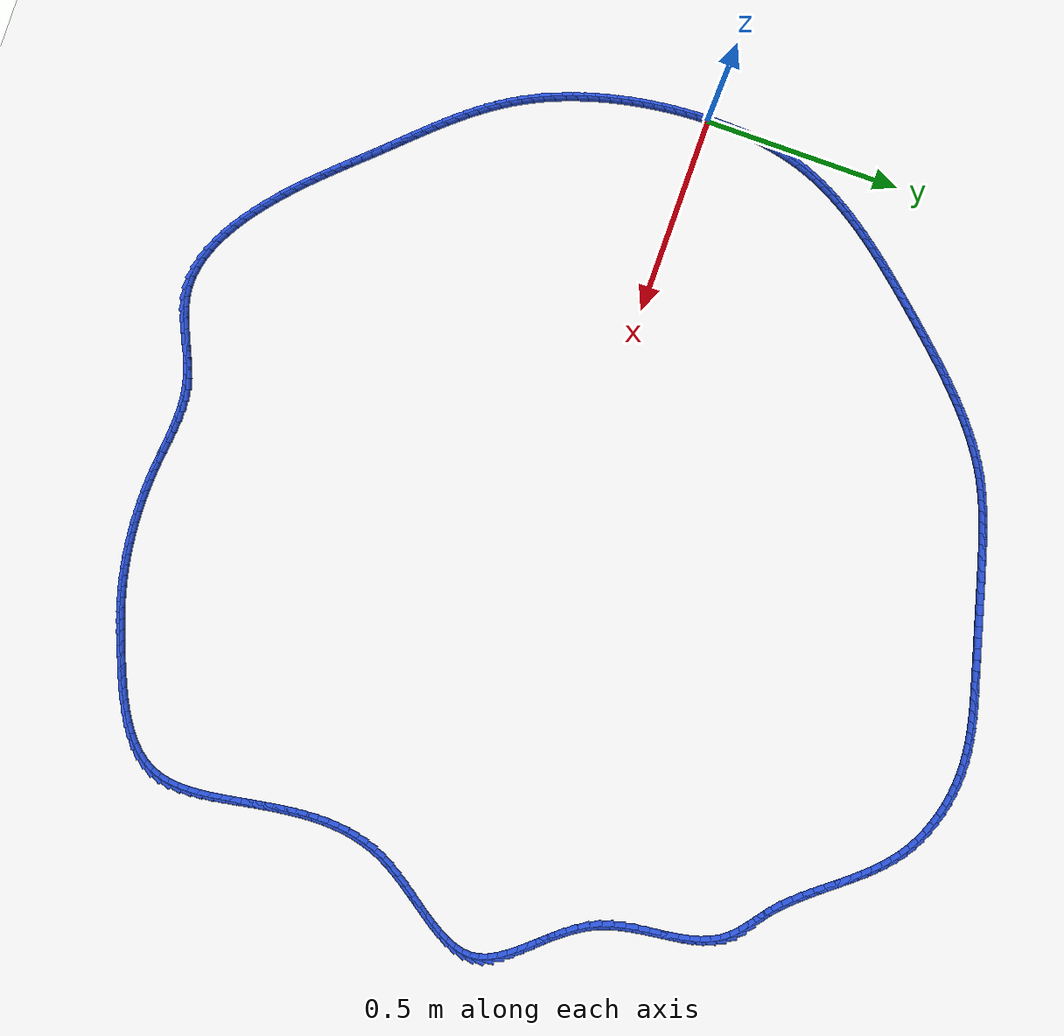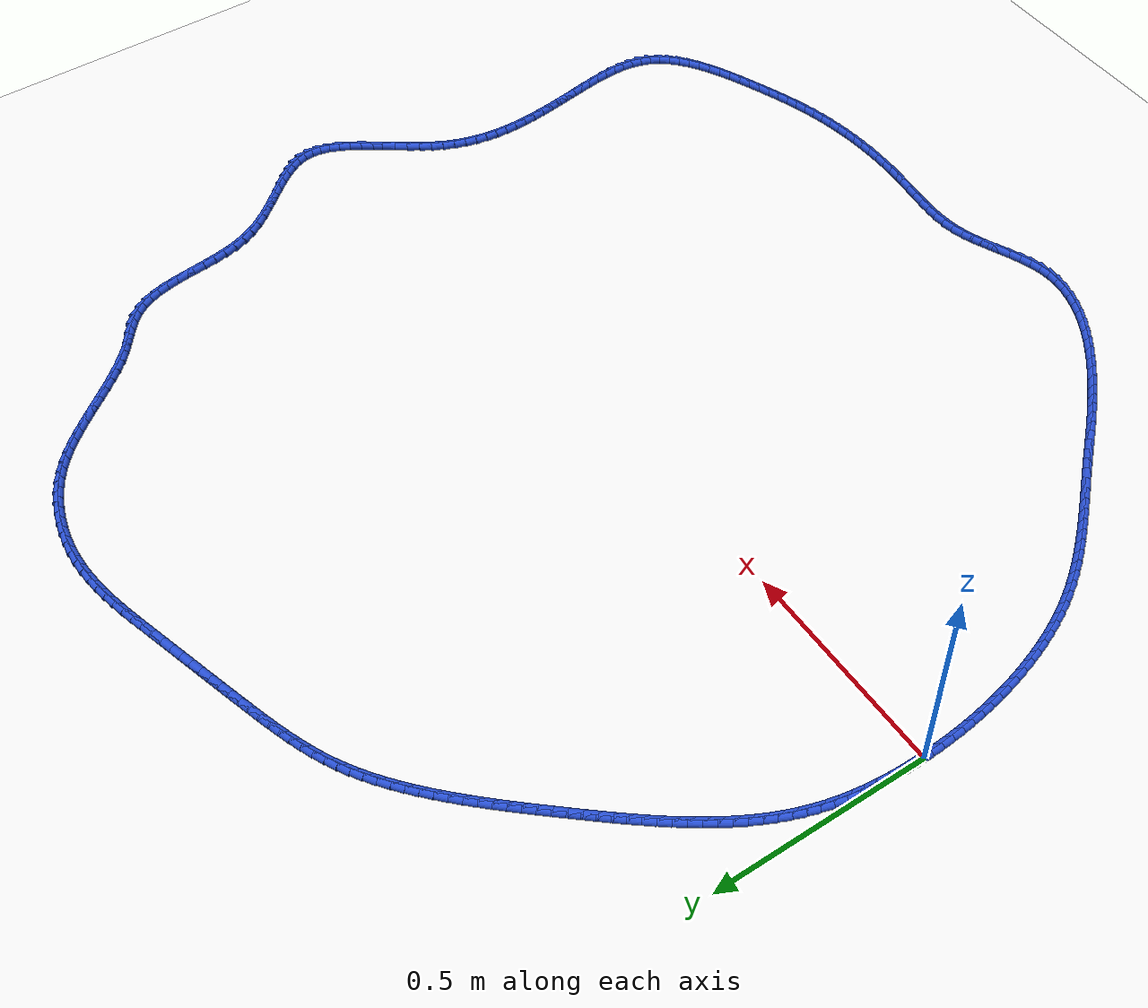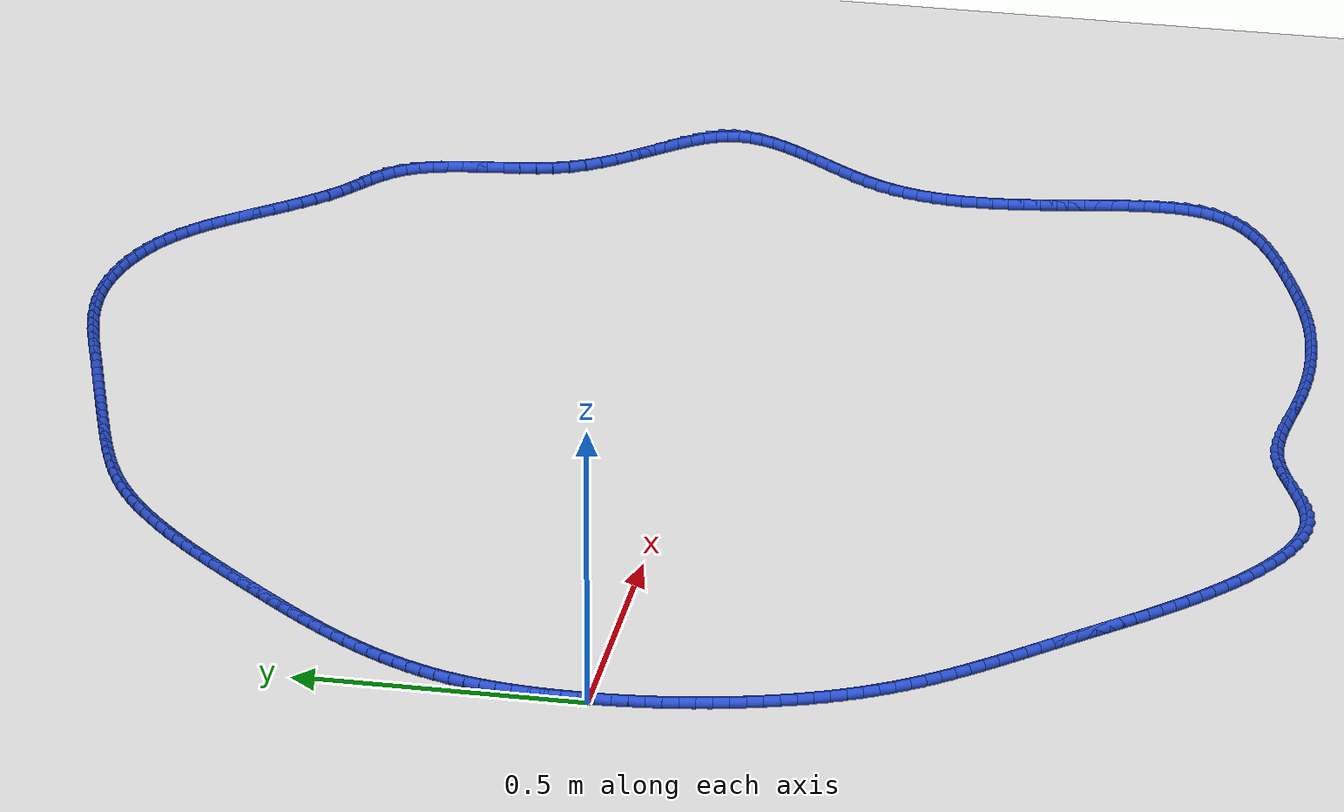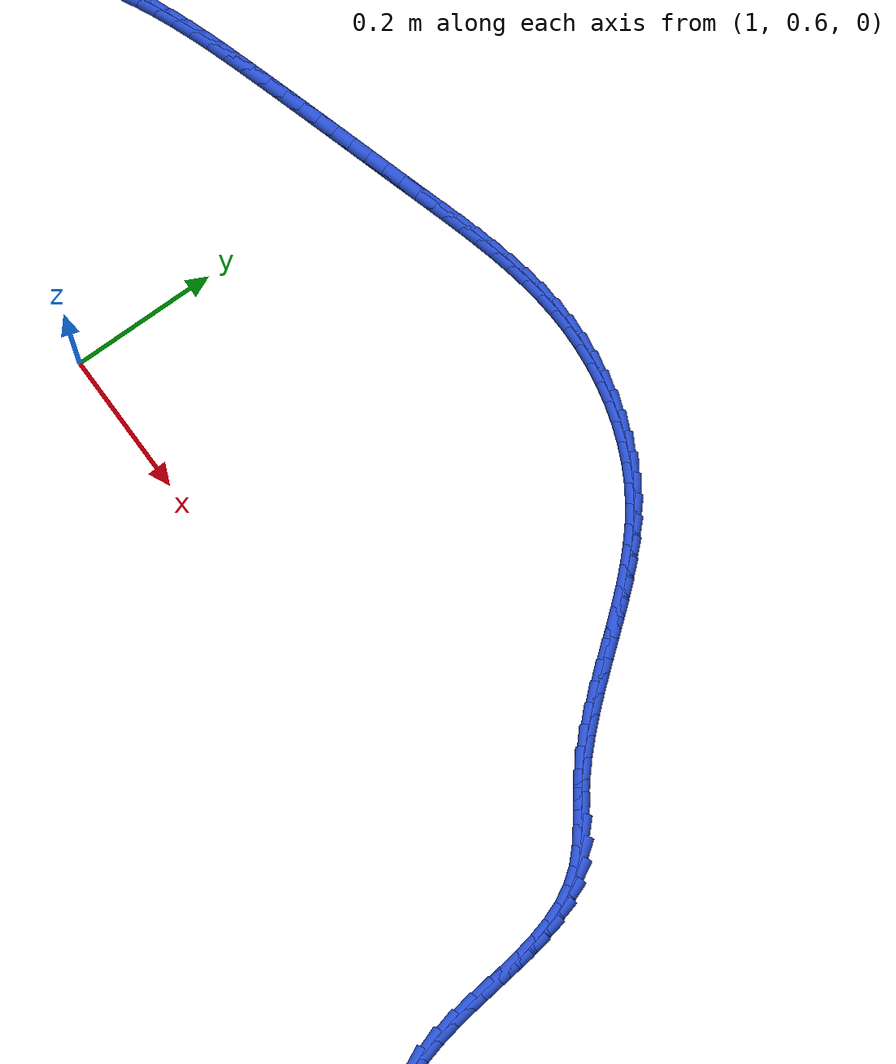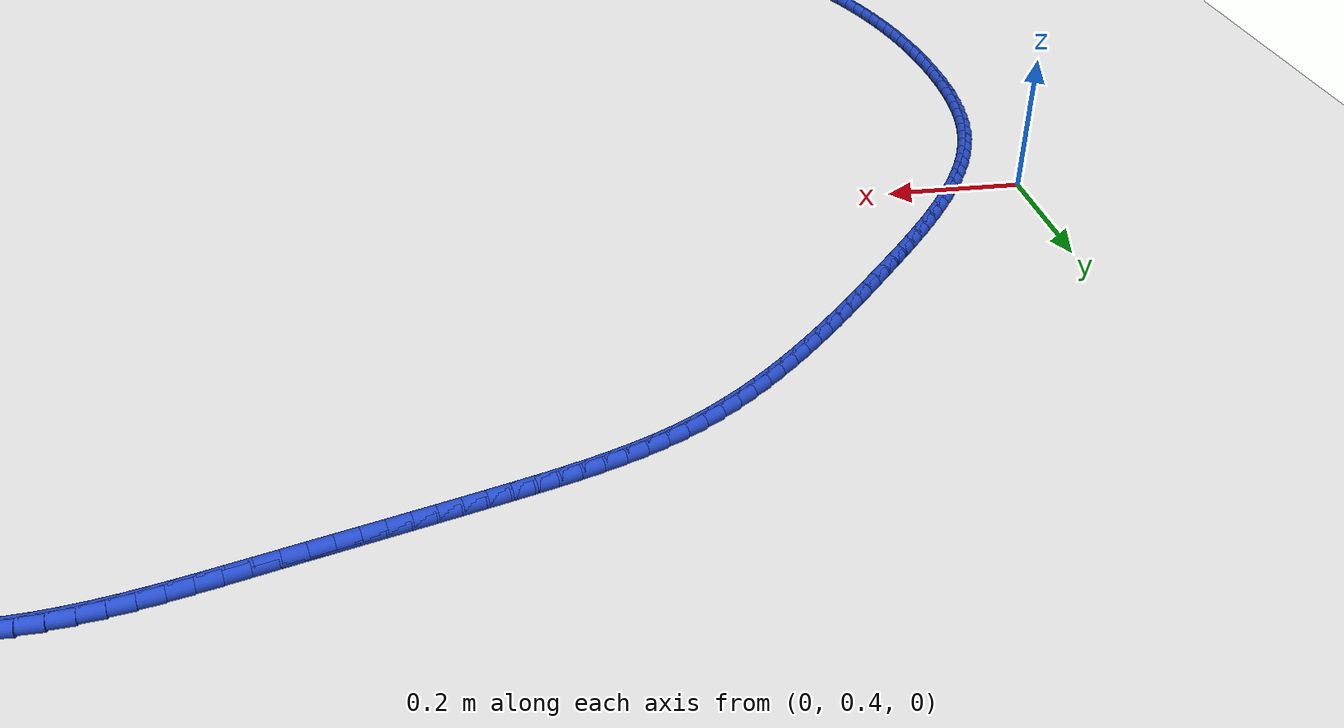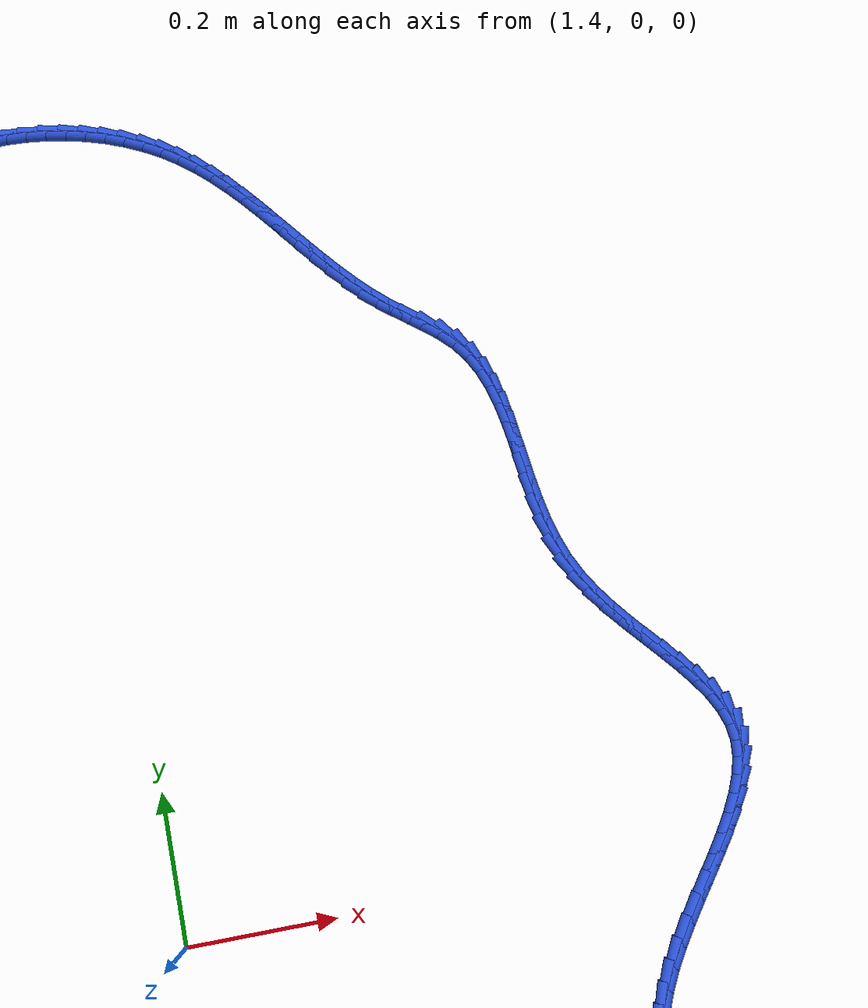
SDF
<sdf version="1.6">
 <world name="default">
  <light name="sun" type="directional">
   <pose>0 0 10 0 -0 0</pose>
   <diffuse>0.8 0.8 0.8 1</diffuse>
   <specular>0.2 0.2 0.2 1</specular>
   <attenuation>
    <range>1000</range>
    <constant>0.9</constant>
    <linear>0.01</linear>
    <quadratic>0.001</quadratic>
   </attenuation>
   <direction>-0.5 0.1 -0.9</direction>
  </light>
  <model name="ground_plane">
   <static>1</static>
   <link name="link">
    <collision name="collision">
     <geometry><plane><normal>0 0 1</normal><size>100 100</size></plane></geometry>
     <surface><friction><ode><mu>100</mu><mu2>50</mu2></ode></friction></surface>
    </collision>
    <visual name="visual">
     <cast_shadows>0</cast_shadows>
     <geometry><plane><normal>0 0 1</normal><size>100 100</size></plane></geometry>
     <material>
      <script><uri>file://media/materials/scripts/gazebo.material</uri><name>Gazebo/WhiteGlow</name></script>
     </material>
    </visual>
   </link>
  </model>
  <gravity>0 0 -9.8</gravity>
  <magnetic_field>6e-06 2.3e-05 -4.2e-05</magnetic_field>
  <atmosphere type="adiabatic"/>
  <physics name="default_physics" default="0" type="ode">
   <max_step_size>0.001</max_step_size>
   <real_time_factor>1</real_time_factor>
   <real_time_update_rate>1000</real_time_update_rate>
  </physics>
  <scene><ambient>0.4 0.4 0.4 1</ambient><background>0.7 0.7 0.7 1</background><shadows>1</shadows></scene>
  <spherical_coordinates>
   <surface_model>EARTH_WGS84</surface_model>
   <latitude_deg>0</latitude_deg>
   <longitude_deg>0</longitude_deg>
   <elevation>0</elevation>
   <heading_deg>0</heading_deg>
  </spherical_coordinates>
  <model name="line">
   <link name="link_0">
    <pose>-1.0842021724855044e-17 -4.85722573273506e-17 0.01 0 1.57 -1.567138101349433</pose>
    <collision name="collision">
     <geometry><cylinder><radius>0.01</radius><length>0.08</length></cylinder></geometry>
    </collision>
    <visual name="visual">
     <material>
      <script><name>Gazebo/Blue</name><uri>file://media/materials/scripts/gazebo.material</uri></script>
     </material>
     <geometry><cylinder><radius>0.01</radius><length>0.08</length></cylinder></geometry>
    </visual>
   </link>
   <link name="link_1">
    <pose>-0.0001018480231743179 0.027840703193754954 0.01 0 1.57 1.5487937625036847</pose>
    <collision name="collision">
     <geometry><cylinder><radius>0.01</radius><length>0.08</length></cylinder></geometry>
    </collision>
    <visual name="visual">
     <material>
      <script><name>Gazebo/Blue</name><uri>file://media/materials/scripts/gazebo.material</uri></script>
     </material>
     <geometry><cylinder><radius>0.01</radius><length>0.08</length></cylinder></geometry>
    </visual>
   </link>
   <link name="link_2">
    <pose>0.0005114483140669621 0.055710062315789136 0.01 0 1.57 1.5206134481660152</pose>
    <collision name="collision">
     <geometry><cylinder><radius>0.01</radius><length>0.08</length></cylinder></geometry>
    </collision>
    <visual name="visual">
     <material>
      <script><name>Gazebo/Blue</name><uri>file://media/materials/scripts/gazebo.material</uri></script>
     </material>
     <geometry><cylinder><radius>0.01</radius><length>0.08</length></cylinder></geometry>
    </visual>
   </link>
   <link name="link_3">
    <pose>0.0019094863454247432 0.08354553733821796 0.01 0 1.57 1.4897752996863332</pose>
    <collision name="collision">
     <geometry><cylinder><radius>0.01</radius><length>0.08</length></cylinder></geometry>
    </collision>
    <visual name="visual">
     <material>
      <script><name>Gazebo/Blue</name><uri>file://media/materials/scripts/gazebo.material</uri></script>
     </material>
     <geometry><cylinder><radius>0.01</radius><length>0.08</length></cylinder></geometry>
    </visual>
   </link>
   <link name="link_4">
    <pose>0.004161863404599926 0.11128458823315666 0.01 0 1.57 1.4561345698130728</pose>
    <collision name="collision">
     <geometry><cylinder><radius>0.01</radius><length>0.08</length></cylinder></geometry>
    </collision>
    <visual name="visual">
     <material>
      <script><name>Gazebo/Blue</name><uri>file://media/materials/scripts/gazebo.material</uri></script>
     </material>
     <geometry><cylinder><radius>0.01</radius><length>0.08</length></cylinder></geometry>
    </visual>
   </link>
   <link name="link_5">
    <pose>0.007338176825293422 0.13886467497272076 0.01 0 1.57 1.4195457635117201</pose>
    <collision name="collision">
     <geometry><cylinder><radius>0.01</radius><length>0.08</length></cylinder></geometry>
    </collision>
    <visual name="visual">
     <material>
      <script><name>Gazebo/Blue</name><uri>file://media/materials/scripts/gazebo.material</uri></script>
     </material>
     <geometry><cylinder><radius>0.01</radius><length>0.08</length></cylinder></geometry>
    </visual>
   </link>
   <link name="link_6">
    <pose>0.011508023941206137 0.1662232575290255 0.01 0 1.57 1.3798701712815957</pose>
    <collision name="collision">
     <geometry><cylinder><radius>0.01</radius><length>0.08</length></cylinder></geometry>
    </collision>
    <visual name="visual">
     <material>
      <script><name>Gazebo/Blue</name><uri>file://media/materials/scripts/gazebo.material</uri></script>
     </material>
     <geometry><cylinder><radius>0.01</radius><length>0.08</length></cylinder></geometry>
    </visual>
   </link>
   <link name="link_7">
    <pose>0.016741002086038976 0.19329779587418625 0.01 0 1.57 1.336985593954813</pose>
    <collision name="collision">
     <geometry><cylinder><radius>0.01</radius><length>0.08</length></cylinder></geometry>
    </collision>
    <visual name="visual">
     <material>
      <script><name>Gazebo/Blue</name><uri>file://media/materials/scripts/gazebo.material</uri></script>
     </material>
     <geometry><cylinder><radius>0.01</radius><length>0.08</length></cylinder></geometry>
    </visual>
   </link>
   <link name="link_8">
    <pose>0.023106708593492856 0.22002574998031854 0.01 0 1.57 1.2907984733065927</pose>
    <collision name="collision">
     <geometry><cylinder><radius>0.01</radius><length>0.08</length></cylinder></geometry>
    </collision>
    <visual name="visual">
     <material>
      <script><name>Gazebo/Blue</name><uri>file://media/materials/scripts/gazebo.material</uri></script>
     </material>
     <geometry><cylinder><radius>0.01</radius><length>0.08</length></cylinder></geometry>
    </visual>
   </link>
   <link name="link_9">
    <pose>0.03067474079726868 0.24634457981953753 0.01 0 1.57 1.2420383899572776</pose>
    <collision name="collision">
     <geometry><cylinder><radius>0.01</radius><length>0.08</length></cylinder></geometry>
    </collision>
    <visual name="visual">
     <material>
      <script><name>Gazebo/Blue</name><uri>file://media/materials/scripts/gazebo.material</uri></script>
     </material>
     <geometry><cylinder><radius>0.01</radius><length>0.08</length></cylinder></geometry>
    </visual>
   </link>
   <link name="link_10">
    <pose>0.039495733256411876 0.2722021534968775 0.01 0 1.57 1.1948599811339922</pose>
    <collision name="collision">
     <geometry><cylinder><radius>0.01</radius><length>0.08</length></cylinder></geometry>
    </collision>
    <visual name="visual">
     <material>
      <script><name>Gazebo/Blue</name><uri>file://media/materials/scripts/gazebo.material</uri></script>
     </material>
     <geometry><cylinder><radius>0.01</radius><length>0.08</length></cylinder></geometry>
    </visual>
   </link>
   <link name="link_11">
    <pose>0.04952084665664499 0.2976009375247422 0.01 0 1.57 1.1507527885234596</pose>
    <collision name="collision">
     <geometry><cylinder><radius>0.01</radius><length>0.08</length></cylinder></geometry>
    </collision>
    <visual name="visual">
     <material>
      <script><name>Gazebo/Blue</name><uri>file://media/materials/scripts/gazebo.material</uri></script>
     </material>
     <geometry><cylinder><radius>0.01</radius><length>0.08</length></cylinder></geometry>
    </visual>
   </link>
   <link name="link_12">
    <pose>0.06066873592587018 0.32256123991047303 0.01 0 1.57 1.1098176480591977</pose>
    <collision name="collision">
     <geometry><cylinder><radius>0.01</radius><length>0.08</length></cylinder></geometry>
    </collision>
    <visual name="visual">
     <material>
      <script><name>Gazebo/Blue</name><uri>file://media/materials/scripts/gazebo.material</uri></script>
     </material>
     <geometry><cylinder><radius>0.01</radius><length>0.08</length></cylinder></geometry>
    </visual>
   </link>
   <link name="link_13">
    <pose>0.07285803767800553 0.3471033787134417 0.01 0 1.57 1.0720966619897865</pose>
    <collision name="collision">
     <geometry><cylinder><radius>0.01</radius><length>0.08</length></cylinder></geometry>
    </collision>
    <visual name="visual">
     <material>
      <script><name>Gazebo/Blue</name><uri>file://media/materials/scripts/gazebo.material</uri></script>
     </material>
     <geometry><cylinder><radius>0.01</radius><length>0.08</length></cylinder></geometry>
    </visual>
   </link>
   <link name="link_14">
    <pose>0.0860073885269689 0.3712476719930197 0.01 0 1.57 1.037586057258967</pose>
    <collision name="collision">
     <geometry><cylinder><radius>0.01</radius><length>0.08</length></cylinder></geometry>
    </collision>
    <visual name="visual">
     <material>
      <script><name>Gazebo/Blue</name><uri>file://media/materials/scripts/gazebo.material</uri></script>
     </material>
     <geometry><cylinder><radius>0.01</radius><length>0.08</length></cylinder></geometry>
    </visual>
   </link>
   <link name="link_15">
    <pose>0.10003542508667838 0.3950144378085786 0.01 0 1.57 1.006248077376711</pose>
    <collision name="collision">
     <geometry><cylinder><radius>0.01</radius><length>0.08</length></cylinder></geometry>
    </collision>
    <visual name="visual">
     <material>
      <script><name>Gazebo/Blue</name><uri>file://media/materials/scripts/gazebo.material</uri></script>
     </material>
     <geometry><cylinder><radius>0.01</radius><length>0.08</length></cylinder></geometry>
    </visual>
   </link>
   <link name="link_16">
    <pose>0.11486078397105197 0.41842399421949006 0.01 0 1.57 0.9780218718568917</pose>
    <collision name="collision">
     <geometry><cylinder><radius>0.01</radius><length>0.08</length></cylinder></geometry>
    </collision>
    <visual name="visual">
     <material>
      <script><name>Gazebo/Blue</name><uri>file://media/materials/scripts/gazebo.material</uri></script>
     </material>
     <geometry><cylinder><radius>0.01</radius><length>0.08</length></cylinder></geometry>
    </visual>
   </link>
   <link name="link_17">
    <pose>0.13040210179400769 0.44149665928512566 0.01 0 1.57 0.9528329684012898</pose>
    <collision name="collision">
     <geometry><cylinder><radius>0.01</radius><length>0.08</length></cylinder></geometry>
    </collision>
    <visual name="visual">
     <material>
      <script><name>Gazebo/Blue</name><uri>file://media/materials/scripts/gazebo.material</uri></script>
     </material>
     <geometry><cylinder><radius>0.01</radius><length>0.08</length></cylinder></geometry>
    </visual>
   </link>
   <link name="link_18">
    <pose>0.14657801516946348 0.4642527510648569 0.01 0 1.57 0.9306011984447259</pose>
    <collision name="collision">
     <geometry><cylinder><radius>0.01</radius><length>0.08</length></cylinder></geometry>
    </collision>
    <visual name="visual">
     <material>
      <script><name>Gazebo/Blue</name><uri>file://media/materials/scripts/gazebo.material</uri></script>
     </material>
     <geometry><cylinder><radius>0.01</radius><length>0.08</length></cylinder></geometry>
    </visual>
   </link>
   <link name="link_19">
    <pose>0.1633071607113373 0.4867125876180554 0.01 0 1.57 0.9112471377221855</pose>
    <collision name="collision">
     <geometry><cylinder><radius>0.01</radius><length>0.08</length></cylinder></geometry>
    </collision>
    <visual name="visual">
     <material>
      <script><name>Gazebo/Blue</name><uri>file://media/materials/scripts/gazebo.material</uri></script>
     </material>
     <geometry><cylinder><radius>0.01</radius><length>0.08</length></cylinder></geometry>
    </visual>
   </link>
   <link name="link_20">
    <pose>0.18050817503354735 0.5088964870040931 0.01 0 1.57 0.8946972336841649</pose>
    <collision name="collision">
     <geometry><cylinder><radius>0.01</radius><length>0.08</length></cylinder></geometry>
    </collision>
    <visual name="visual">
     <material>
      <script><name>Gazebo/Blue</name><uri>file://media/materials/scripts/gazebo.material</uri></script>
     </material>
     <geometry><cylinder><radius>0.01</radius><length>0.08</length></cylinder></geometry>
    </visual>
   </link>
   <link name="link_21">
    <pose>0.19809969475001146 0.530824767282341 0.01 0 1.57 0.8808878413360367</pose>
    <collision name="collision">
     <geometry><cylinder><radius>0.01</radius><length>0.08</length></cylinder></geometry>
    </collision>
    <visual name="visual">
     <material>
      <script><name>Gazebo/Blue</name><uri>file://media/materials/scripts/gazebo.material</uri></script>
     </material>
     <geometry><cylinder><radius>0.01</radius><length>0.08</length></cylinder></geometry>
    </visual>
   </link>
   <link name="link_22">
    <pose>0.21600035647464755 0.5525177465121708 0.01 0 1.57 0.8697683984491581</pose>
    <collision name="collision">
     <geometry><cylinder><radius>0.01</radius><length>0.08</length></cylinder></geometry>
    </collision>
    <visual name="visual">
     <material>
      <script><name>Gazebo/Blue</name><uri>file://media/materials/scripts/gazebo.material</uri></script>
     </material>
     <geometry><cylinder><radius>0.01</radius><length>0.08</length></cylinder></geometry>
    </visual>
   </link>
   <link name="link_23">
    <pose>0.23412879682137389 0.5739957427529544 0.01 0 1.57 0.8613039562555125</pose>
    <collision name="collision">
     <geometry><cylinder><radius>0.01</radius><length>0.08</length></cylinder></geometry>
    </collision>
    <visual name="visual">
     <material>
      <script><name>Gazebo/Blue</name><uri>file://media/materials/scripts/gazebo.material</uri></script>
     </material>
     <geometry><cylinder><radius>0.01</radius><length>0.08</length></cylinder></geometry>
    </visual>
   </link>
   <link name="link_24">
    <pose>0.2524036524041083 0.5952790740640631 0.01 0 1.57 0.8554772540911887</pose>
    <collision name="collision">
     <geometry><cylinder><radius>0.01</radius><length>0.08</length></cylinder></geometry>
    </collision>
    <visual name="visual">
     <material>
      <script><name>Gazebo/Blue</name><uri>file://media/materials/scripts/gazebo.material</uri></script>
     </material>
     <geometry><cylinder><radius>0.01</radius><length>0.08</length></cylinder></geometry>
    </visual>
   </link>
   <link name="link_25">
    <pose>0.2707435598367689 0.616388058504869 0.01 0 1.57 0.8521937747427385</pose>
    <collision name="collision">
     <geometry><cylinder><radius>0.01</radius><length>0.08</length></cylinder></geometry>
    </collision>
    <visual name="visual">
     <material>
      <script><name>Gazebo/Blue</name><uri>file://media/materials/scripts/gazebo.material</uri></script>
     </material>
     <geometry><cylinder><radius>0.01</radius><length>0.08</length></cylinder></geometry>
    </visual>
   </link>
   <link name="link_26">
    <pose>0.2890701103326086 0.6373423028204352 0.01 0 1.57 0.8492410949826225</pose>
    <collision name="collision">
     <geometry><cylinder><radius>0.01</radius><length>0.08</length></cylinder></geometry>
    </collision>
    <visual name="visual">
     <material>
      <script><name>Gazebo/Blue</name><uri>file://media/materials/scripts/gazebo.material</uri></script>
     </material>
     <geometry><cylinder><radius>0.01</radius><length>0.08</length></cylinder></geometry>
    </visual>
   </link>
   <link name="link_27">
    <pose>0.30737285353726645 0.6581450528893269 0.01 0 1.57 0.8443859554230504</pose>
    <collision name="collision">
     <geometry><cylinder><radius>0.01</radius><length>0.08</length></cylinder></geometry>
    </collision>
    <visual name="visual">
     <material>
      <script><name>Gazebo/Blue</name><uri>file://media/materials/scripts/gazebo.material</uri></script>
     </material>
     <geometry><cylinder><radius>0.01</radius><length>0.08</length></cylinder></geometry>
    </visual>
   </link>
   <link name="link_28">
    <pose>0.3257092989997319 0.6787831933694779 0.01 0 1.57 0.837525633527093</pose>
    <collision name="collision">
     <geometry><cylinder><radius>0.01</radius><length>0.08</length></cylinder></geometry>
    </collision>
    <visual name="visual">
     <material>
      <script><name>Gazebo/Blue</name><uri>file://media/materials/scripts/gazebo.material</uri></script>
     </material>
     <geometry><cylinder><radius>0.01</radius><length>0.08</length></cylinder></geometry>
    </visual>
   </link>
   <link name="link_29">
    <pose>0.3441399111625224 0.6992428975336877 0.01 0 1.57 0.8286679622097102</pose>
    <collision name="collision">
     <geometry><cylinder><radius>0.01</radius><length>0.08</length></cylinder></geometry>
    </collision>
    <visual name="visual">
     <material>
      <script><name>Gazebo/Blue</name><uri>file://media/materials/scripts/gazebo.material</uri></script>
     </material>
     <geometry><cylinder><radius>0.01</radius><length>0.08</length></cylinder></geometry>
    </visual>
   </link>
   <link name="link_30">
    <pose>0.36272515446815506 0.7195103386547561 0.01 0 1.57 0.817835511066305</pose>
    <collision name="collision">
     <geometry><cylinder><radius>0.01</radius><length>0.08</length></cylinder></geometry>
    </collision>
    <visual name="visual">
     <material>
      <script><name>Gazebo/Blue</name><uri>file://media/materials/scripts/gazebo.material</uri></script>
     </material>
     <geometry><cylinder><radius>0.01</radius><length>0.08</length></cylinder></geometry>
    </visual>
   </link>
   <link name="link_31">
    <pose>0.3815254933591474 0.7395716900054821 0.01 0 1.57 0.8050664485522597</pose>
    <collision name="collision">
     <geometry><cylinder><radius>0.01</radius><length>0.08</length></cylinder></geometry>
    </collision>
    <visual name="visual">
     <material>
      <script><name>Gazebo/Blue</name><uri>file://media/materials/scripts/gazebo.material</uri></script>
     </material>
     <geometry><cylinder><radius>0.01</radius><length>0.08</length></cylinder></geometry>
    </visual>
   </link>
   <link name="link_32">
    <pose>0.400601392278017 0.7594131248586659 0.01 0 1.57 0.7904152963569561</pose>
    <collision name="collision">
     <geometry><cylinder><radius>0.01</radius><length>0.08</length></cylinder></geometry>
    </collision>
    <visual name="visual">
     <material>
      <script><name>Gazebo/Blue</name><uri>file://media/materials/scripts/gazebo.material</uri></script>
     </material>
     <geometry><cylinder><radius>0.01</radius><length>0.08</length></cylinder></geometry>
    </visual>
   </link>
   <link name="link_33">
    <pose>0.42001331566728095 0.7790208164871066 0.01 0 1.57 0.7737581388340069</pose>
    <collision name="collision">
     <geometry><cylinder><radius>0.01</radius><length>0.08</length></cylinder></geometry>
    </collision>
    <visual name="visual">
     <material>
      <script><name>Gazebo/Blue</name><uri>file://media/materials/scripts/gazebo.material</uri></script>
     </material>
     <geometry><cylinder><radius>0.01</radius><length>0.08</length></cylinder></geometry>
    </visual>
   </link>
   <link name="link_34">
    <pose>0.43981696849531143 0.7983687236123765 0.01 0 1.57 0.7541543347570773</pose>
    <collision name="collision">
     <geometry><cylinder><radius>0.01</radius><length>0.08</length></cylinder></geometry>
    </collision>
    <visual name="visual">
     <material>
      <script><name>Gazebo/Blue</name><uri>file://media/materials/scripts/gazebo.material</uri></script>
     </material>
     <geometry><cylinder><radius>0.01</radius><length>0.08</length></cylinder></geometry>
    </visual>
   </link>
   <link name="link_35">
    <pose>0.4600444014446152 0.8173700994079949 0.01 0 1.57 0.731234655228262</pose>
    <collision name="collision">
     <geometry><cylinder><radius>0.01</radius><length>0.08</length></cylinder></geometry>
    </collision>
    <visual name="visual">
     <material>
      <script><name>Gazebo/Blue</name><uri>file://media/materials/scripts/gazebo.material</uri></script>
     </material>
     <geometry><cylinder><radius>0.01</radius><length>0.08</length></cylinder></geometry>
    </visual>
   </link>
   <link name="link_36">
    <pose>0.4807203306520186 0.8359193739209727 0.01 0 1.57 0.7049009868577691</pose>
    <collision name="collision">
     <geometry><cylinder><radius>0.01</radius><length>0.08</length></cylinder></geometry>
    </collision>
    <visual name="visual">
     <material>
      <script><name>Gazebo/Blue</name><uri>file://media/materials/scripts/gazebo.material</uri></script>
     </material>
     <geometry><cylinder><radius>0.01</radius><length>0.08</length></cylinder></geometry>
    </visual>
   </link>
   <link name="link_37">
    <pose>0.5018694700160675 0.8539109714540767 0.01 0 1.57 0.6750421024260883</pose>
    <collision name="collision">
     <geometry><cylinder><radius>0.01</radius><length>0.08</length></cylinder></geometry>
    </collision>
    <visual name="visual">
     <material>
      <script><name>Gazebo/Blue</name><uri>file://media/materials/scripts/gazebo.material</uri></script>
     </material>
     <geometry><cylinder><radius>0.01</radius><length>0.08</length></cylinder></geometry>
    </visual>
   </link>
   <link name="link_38">
    <pose>0.5235165334353089 0.8712393163100739 0.01 0 1.57 0.6415421392414047</pose>
    <collision name="collision">
     <geometry><cylinder><radius>0.01</radius><length>0.08</length></cylinder></geometry>
    </collision>
    <visual name="visual">
     <material>
      <script><name>Gazebo/Blue</name><uri>file://media/materials/scripts/gazebo.material</uri></script>
     </material>
     <geometry><cylinder><radius>0.01</radius><length>0.08</length></cylinder></geometry>
    </visual>
   </link>
   <link name="link_39">
    <pose>0.5456862348082888 0.8877988327917317 0.01 0 1.57 0.6042914383586098</pose>
    <collision name="collision">
     <geometry><cylinder><radius>0.01</radius><length>0.08</length></cylinder></geometry>
    </collision>
    <visual name="visual">
     <material>
      <script><name>Gazebo/Blue</name><uri>file://media/materials/scripts/gazebo.material</uri></script>
     </material>
     <geometry><cylinder><radius>0.01</radius><length>0.08</length></cylinder></geometry>
    </visual>
   </link>
   <link name="link_40">
    <pose>0.5684032880335538 0.9034839452018167 0.01 0 1.57 0.5632000857672532</pose>
    <collision name="collision">
     <geometry><cylinder><radius>0.01</radius><length>0.08</length></cylinder></geometry>
    </collision>
    <visual name="visual">
     <material>
      <script><name>Gazebo/Blue</name><uri>file://media/materials/scripts/gazebo.material</uri></script>
     </material>
     <geometry><cylinder><radius>0.01</radius><length>0.08</length></cylinder></geometry>
    </visual>
   </link>
   <link name="link_41">
    <pose>0.59169240700965 0.918189077843096 0.01 0 1.57 0.5182143457511004</pose>
    <collision name="collision">
     <geometry><cylinder><radius>0.01</radius><length>0.08</length></cylinder></geometry>
    </collision>
    <visual name="visual">
     <material>
      <script><name>Gazebo/Blue</name><uri>file://media/materials/scripts/gazebo.material</uri></script>
     </material>
     <geometry><cylinder><radius>0.01</radius><length>0.08</length></cylinder></geometry>
    </visual>
   </link>
   <link name="link_42">
    <pose>0.6155783056276274 0.9318086550353273 0.01 0 1.57 0.47098109817317413</pose>
    <collision name="collision">
     <geometry><cylinder><radius>0.01</radius><length>0.08</length></cylinder></geometry>
    </collision>
    <visual name="visual">
     <material>
      <script><name>Gazebo/Blue</name><uri>file://media/materials/scripts/gazebo.material</uri></script>
     </material>
     <geometry><cylinder><radius>0.01</radius><length>0.08</length></cylinder></geometry>
    </visual>
   </link>
   <link name="link_43">
    <pose>0.6400674185866904 0.9442785300454983 0.01 0 1.57 0.4280184535754709</pose>
    <collision name="collision">
     <geometry><cylinder><radius>0.01</radius><length>0.08</length></cylinder></geometry>
    </collision>
    <visual name="visual">
     <material>
      <script><name>Gazebo/Blue</name><uri>file://media/materials/scripts/gazebo.material</uri></script>
     </material>
     <geometry><cylinder><radius>0.01</radius><length>0.08</length></cylinder></geometry>
    </visual>
   </link>
   <link name="link_44">
    <pose>0.6650946873046958 0.9556965923731204 0.01 0 1.57 0.3909691670549991</pose>
    <collision name="collision">
     <geometry><cylinder><radius>0.01</radius><length>0.08</length></cylinder></geometry>
    </collision>
    <visual name="visual">
     <material>
      <script><name>Gazebo/Blue</name><uri>file://media/materials/scripts/gazebo.material</uri></script>
     </material>
     <geometry><cylinder><radius>0.01</radius><length>0.08</length></cylinder></geometry>
    </visual>
   </link>
   <link name="link_45">
    <pose>0.690577576778318 0.9662003410221667 0.01 0 1.57 0.3598194669974591</pose>
    <collision name="collision">
     <geometry><cylinder><radius>0.01</radius><length>0.08</length></cylinder></geometry>
    </collision>
    <visual name="visual">
     <material>
      <script><name>Gazebo/Blue</name><uri>file://media/materials/scripts/gazebo.material</uri></script>
     </material>
     <geometry><cylinder><radius>0.01</radius><length>0.08</length></cylinder></geometry>
    </visual>
   </link>
   <link name="link_46">
    <pose>0.7164335520042314 0.9759272749966104 0.01 0 1.57 0.33450394375181675</pose>
    <collision name="collision">
     <geometry><cylinder><radius>0.01</radius><length>0.08</length></cylinder></geometry>
    </collision>
    <visual name="visual">
     <material>
      <script><name>Gazebo/Blue</name><uri>file://media/materials/scripts/gazebo.material</uri></script>
     </material>
     <geometry><cylinder><radius>0.01</radius><length>0.08</length></cylinder></geometry>
    </visual>
   </link>
   <link name="link_47">
    <pose>0.7425800779791099 0.9850148933004245 0.01 0 1.57 0.31493787355434993</pose>
    <collision name="collision">
     <geometry><cylinder><radius>0.01</radius><length>0.08</length></cylinder></geometry>
    </collision>
    <visual name="visual">
     <material>
      <script><name>Gazebo/Blue</name><uri>file://media/materials/scripts/gazebo.material</uri></script>
     </material>
     <geometry><cylinder><radius>0.01</radius><length>0.08</length></cylinder></geometry>
    </visual>
   </link>
   <link name="link_48">
    <pose>0.7689346196996277 0.9936006949375817 0.01 0 1.57 0.3010423763997181</pose>
    <collision name="collision">
     <geometry><cylinder><radius>0.01</radius><length>0.08</length></cylinder></geometry>
    </collision>
    <visual name="visual">
     <material>
      <script><name>Gazebo/Blue</name><uri>file://media/materials/scripts/gazebo.material</uri></script>
     </material>
     <geometry><cylinder><radius>0.01</radius><length>0.08</length></cylinder></geometry>
    </visual>
   </link>
   <link name="link_49">
    <pose>0.7954146421624592 1.0018221789120556 0.01 0 1.57 0.29276291644287655</pose>
    <collision name="collision">
     <geometry><cylinder><radius>0.01</radius><length>0.08</length></cylinder></geometry>
    </collision>
    <visual name="visual">
     <material>
      <script><name>Gazebo/Blue</name><uri>file://media/materials/scripts/gazebo.material</uri></script>
     </material>
     <geometry><cylinder><radius>0.01</radius><length>0.08</length></cylinder></geometry>
    </visual>
   </link>
   <link name="link_50">
    <pose>0.8219376103642783 1.0098168442278193 0.01 0 1.57 0.2892614484721174</pose>
    <collision name="collision">
     <geometry><cylinder><radius>0.01</radius><length>0.08</length></cylinder></geometry>
    </collision>
    <visual name="visual">
     <material>
      <script><name>Gazebo/Blue</name><uri>file://media/materials/scripts/gazebo.material</uri></script>
     </material>
     <geometry><cylinder><radius>0.01</radius><length>0.08</length></cylinder></geometry>
    </visual>
   </link>
   <link name="link_51">
    <pose>0.8484354526333956 1.0177028311336134 0.01 0 1.57 0.28704382290385205</pose>
    <collision name="collision">
     <geometry><cylinder><radius>0.01</radius><length>0.08</length></cylinder></geometry>
    </collision>
    <visual name="visual">
     <material>
      <script><name>Gazebo/Blue</name><uri>file://media/materials/scripts/gazebo.material</uri></script>
     </material>
     <geometry><cylinder><radius>0.01</radius><length>0.08</length></cylinder></geometry>
    </visual>
   </link>
   <link name="link_52">
    <pose>0.8749018591012089 1.0255156134733148 0.01 0 1.57 0.2851813638733168</pose>
    <collision name="collision">
     <geometry><cylinder><radius>0.01</radius><length>0.08</length></cylinder></geometry>
    </collision>
    <visual name="visual">
     <material>
      <script><name>Gazebo/Blue</name><uri>file://media/materials/scripts/gazebo.material</uri></script>
     </material>
     <geometry><cylinder><radius>0.01</radius><length>0.08</length></cylinder></geometry>
    </visual>
   </link>
   <link name="link_53">
    <pose>0.9013470025895353 1.033268603481664 0.01 0 1.57 0.2836782668128358</pose>
    <collision name="collision">
     <geometry><cylinder><radius>0.01</radius><length>0.08</length></cylinder></geometry>
    </collision>
    <visual name="visual">
     <material>
      <script><name>Gazebo/Blue</name><uri>file://media/materials/scripts/gazebo.material</uri></script>
     </material>
     <geometry><cylinder><radius>0.01</radius><length>0.08</length></cylinder></geometry>
    </visual>
   </link>
   <link name="link_54">
    <pose>0.9277810560799484 1.04097521317957 0.01 0 1.57 0.28253768203652496</pose>
    <collision name="collision">
     <geometry><cylinder><radius>0.01</radius><length>0.08</length></cylinder></geometry>
    </collision>
    <visual name="visual">
     <material>
      <script><name>Gazebo/Blue</name><uri>file://media/materials/scripts/gazebo.material</uri></script>
     </material>
     <geometry><cylinder><radius>0.01</radius><length>0.08</length></cylinder></geometry>
    </visual>
   </link>
   <link name="link_55">
    <pose>0.954214192554023 1.0486488545879422 0.01 0 1.57 0.28176169145840424</pose>
    <collision name="collision">
     <geometry><cylinder><radius>0.01</radius><length>0.08</length></cylinder></geometry>
    </collision>
    <visual name="visual">
     <material>
      <script><name>Gazebo/Blue</name><uri>file://media/materials/scripts/gazebo.material</uri></script>
     </material>
     <geometry><cylinder><radius>0.01</radius><length>0.08</length></cylinder></geometry>
    </visual>
   </link>
   <link name="link_56">
    <pose>0.9806565849933325 1.0563029397276897 0.01 0 1.57 0.2813513008971866</pose>
    <collision name="collision">
     <geometry><cylinder><radius>0.01</radius><length>0.08</length></cylinder></geometry>
    </collision>
    <visual name="visual">
     <material>
      <script><name>Gazebo/Blue</name><uri>file://media/materials/scripts/gazebo.material</uri></script>
     </material>
     <geometry><cylinder><radius>0.01</radius><length>0.08</length></cylinder></geometry>
    </visual>
   </link>
   <link name="link_57">
    <pose>1.0071184063794512 1.0639508806197215 0.01 0 1.57 0.28130643890232543</pose>
    <collision name="collision">
     <geometry><cylinder><radius>0.01</radius><length>0.08</length></cylinder></geometry>
    </collision>
    <visual name="visual">
     <material>
      <script><name>Gazebo/Blue</name><uri>file://media/materials/scripts/gazebo.material</uri></script>
     </material>
     <geometry><cylinder><radius>0.01</radius><length>0.08</length></cylinder></geometry>
    </visual>
   </link>
   <link name="link_58">
    <pose>1.0336098296939533 1.0716060892849477 0.01 0 1.57 0.281625962046603</pose>
    <collision name="collision">
     <geometry><cylinder><radius>0.01</radius><length>0.08</length></cylinder></geometry>
    </collision>
    <visual name="visual">
     <material>
      <script><name>Gazebo/Blue</name><uri>file://media/materials/scripts/gazebo.material</uri></script>
     </material>
     <geometry><cylinder><radius>0.01</radius><length>0.08</length></cylinder></geometry>
    </visual>
   </link>
   <link name="link_59">
    <pose>1.0601410279184122 1.0792819777442761 0.01 0 1.57 0.28227147502520206</pose>
    <collision name="collision">
     <geometry><cylinder><radius>0.01</radius><length>0.08</length></cylinder></geometry>
    </collision>
    <visual name="visual">
     <material>
      <script><name>Gazebo/Blue</name><uri>file://media/materials/scripts/gazebo.material</uri></script>
     </material>
     <geometry><cylinder><radius>0.01</radius><length>0.08</length></cylinder></geometry>
    </visual>
   </link>
   <link name="link_60">
    <pose>1.0867222086044612 1.086990925106635 0.01 0 1.57 0.28063739986274855</pose>
    <collision name="collision">
     <geometry><cylinder><radius>0.01</radius><length>0.08</length></cylinder></geometry>
    </collision>
    <visual name="visual">
     <material>
      <script><name>Gazebo/Blue</name><uri>file://media/materials/scripts/gazebo.material</uri></script>
     </material>
     <geometry><cylinder><radius>0.01</radius><length>0.08</length></cylinder></geometry>
    </visual>
   </link>
   <link name="link_61">
    <pose>1.1133660706073067 1.0946708733118404 0.01 0 1.57 0.2724246127013261</pose>
    <collision name="collision">
     <geometry><cylinder><radius>0.01</radius><length>0.08</length></cylinder></geometry>
    </collision>
    <visual name="visual">
     <material>
      <script><name>Gazebo/Blue</name><uri>file://media/materials/scripts/gazebo.material</uri></script>
     </material>
     <geometry><cylinder><radius>0.01</radius><length>0.08</length></cylinder></geometry>
    </visual>
   </link>
   <link name="link_62">
    <pose>1.1400894353934774 1.1021365856074015 0.01 0 1.57 0.2572107848409974</pose>
    <collision name="collision">
     <geometry><cylinder><radius>0.01</radius><length>0.08</length></cylinder></geometry>
    </collision>
    <visual name="visual">
     <material>
      <script><name>Gazebo/Blue</name><uri>file://media/materials/scripts/gazebo.material</uri></script>
     </material>
     <geometry><cylinder><radius>0.01</radius><length>0.08</length></cylinder></geometry>
    </visual>
   </link>
   <link name="link_63">
    <pose>1.1669095114374335 1.1091912619070383 0.01 0 1.57 0.2349369043771384</pose>
    <collision name="collision">
     <geometry><cylinder><radius>0.01</radius><length>0.08</length></cylinder></geometry>
    </collision>
    <visual name="visual">
     <material>
      <script><name>Gazebo/Blue</name><uri>file://media/materials/scripts/gazebo.material</uri></script>
     </material>
     <geometry><cylinder><radius>0.01</radius><length>0.08</length></cylinder></geometry>
    </visual>
   </link>
   <link name="link_64">
    <pose>1.193843507213636 1.1156381021244721 0.01 0 1.57 0.2055241596358322</pose>
    <collision name="collision">
     <geometry><cylinder><radius>0.01</radius><length>0.08</length></cylinder></geometry>
    </collision>
    <visual name="visual">
     <material>
      <script><name>Gazebo/Blue</name><uri>file://media/materials/scripts/gazebo.material</uri></script>
     </material>
     <geometry><cylinder><radius>0.01</radius><length>0.08</length></cylinder></geometry>
    </visual>
   </link>
   <link name="link_65">
    <pose>1.220908631196543 1.1212803061734218 0.01 0 1.57 0.16890723727493465</pose>
    <collision name="collision">
     <geometry><cylinder><radius>0.01</radius><length>0.08</length></cylinder></geometry>
    </collision>
    <visual name="visual">
     <material>
      <script><name>Gazebo/Blue</name><uri>file://media/materials/scripts/gazebo.material</uri></script>
     </material>
     <geometry><cylinder><radius>0.01</radius><length>0.08</length></cylinder></geometry>
    </visual>
   </link>
   <link name="link_66">
    <pose>1.2481220918606164 1.1259210739676084 0.01 0 1.57 0.12507977747997986</pose>
    <collision name="collision">
     <geometry><cylinder><radius>0.01</radius><length>0.08</length></cylinder></geometry>
    </collision>
    <visual name="visual">
     <material>
      <script><name>Gazebo/Blue</name><uri>file://media/materials/scripts/gazebo.material</uri></script>
     </material>
     <geometry><cylinder><radius>0.01</radius><length>0.08</length></cylinder></geometry>
    </visual>
   </link>
   <link name="link_67">
    <pose>1.2755010976803156 1.1293636054207523 0.01 0 1.57 0.07415132518568276</pose>
    <collision name="collision">
     <geometry><cylinder><radius>0.01</radius><length>0.08</length></cylinder></geometry>
    </collision>
    <visual name="visual">
     <material>
      <script><name>Gazebo/Blue</name><uri>file://media/materials/scripts/gazebo.material</uri></script>
     </material>
     <geometry><cylinder><radius>0.01</radius><length>0.08</length></cylinder></geometry>
    </visual>
   </link>
   <link name="link_68">
    <pose>1.303062857130101 1.1314111004465732 0.01 0 1.57 0.0164117200325248</pose>
    <collision name="collision">
     <geometry><cylinder><radius>0.01</radius><length>0.08</length></cylinder></geometry>
    </collision>
    <visual name="visual">
     <material>
      <script><name>Gazebo/Blue</name><uri>file://media/materials/scripts/gazebo.material</uri></script>
     </material>
     <geometry><cylinder><radius>0.01</radius><length>0.08</length></cylinder></geometry>
    </visual>
   </link>
   <link name="link_69">
    <pose>1.3308245786844324 1.1318667589587914 0.01 0 1.57 -0.04645657368198206</pose>
    <collision name="collision">
     <geometry><cylinder><radius>0.01</radius><length>0.08</length></cylinder></geometry>
    </collision>
    <visual name="visual">
     <material>
      <script><name>Gazebo/Blue</name><uri>file://media/materials/scripts/gazebo.material</uri></script>
     </material>
     <geometry><cylinder><radius>0.01</radius><length>0.08</length></cylinder></geometry>
    </visual>
   </link>
   <link name="link_70">
    <pose>1.3587692045144981 1.1305676126438093 0.01 0 1.57 -0.10956556486181751</pose>
    <collision name="collision">
     <geometry><cylinder><radius>0.01</radius><length>0.08</length></cylinder></geometry>
    </collision>
    <visual name="visual">
     <material>
      <script><name>Gazebo/Blue</name><uri>file://media/materials/scripts/gazebo.material</uri></script>
     </material>
     <geometry><cylinder><radius>0.01</radius><length>0.08</length></cylinder></geometry>
    </visual>
   </link>
   <link name="link_71">
    <pose>1.3867376570880983 1.1274909119412262 0.01 0 1.57 -0.1724186300896279</pose>
    <collision name="collision">
     <geometry><cylinder><radius>0.01</radius><length>0.08</length></cylinder></geometry>
    </collision>
    <visual name="visual">
     <material>
      <script><name>Gazebo/Blue</name><uri>file://media/materials/scripts/gazebo.material</uri></script>
     </material>
     <geometry><cylinder><radius>0.01</radius><length>0.08</length></cylinder></geometry>
    </visual>
   </link>
   <link name="link_72">
    <pose>1.4145340708786305 1.1226502287769171 0.01 0 1.57 -0.2358294093577178</pose>
    <collision name="collision">
     <geometry><cylinder><radius>0.01</radius><length>0.08</length></cylinder></geometry>
    </collision>
    <visual name="visual">
     <material>
      <script><name>Gazebo/Blue</name><uri>file://media/materials/scripts/gazebo.material</uri></script>
     </material>
     <geometry><cylinder><radius>0.01</radius><length>0.08</length></cylinder></geometry>
    </visual>
   </link>
   <link name="link_73">
    <pose>1.44196258030062 1.116059135134884 0.01 0 1.57 -0.30060101414818047</pose>
    <collision name="collision">
     <geometry><cylinder><radius>0.01</radius><length>0.08</length></cylinder></geometry>
    </collision>
    <visual name="visual">
     <material>
      <script><name>Gazebo/Blue</name><uri>file://media/materials/scripts/gazebo.material</uri></script>
     </material>
     <geometry><cylinder><radius>0.01</radius><length>0.08</length></cylinder></geometry>
    </visual>
   </link>
   <link name="link_74">
    <pose>1.4688273197685913 1.107731202999129 0.01 0 1.57 -0.36753331716097837</pose>
    <collision name="collision">
     <geometry><cylinder><radius>0.01</radius><length>0.08</length></cylinder></geometry>
    </collision>
    <visual name="visual">
     <material>
      <script><name>Gazebo/Blue</name><uri>file://media/materials/scripts/gazebo.material</uri></script>
     </material>
     <geometry><cylinder><radius>0.01</radius><length>0.08</length></cylinder></geometry>
    </visual>
   </link>
   <link name="link_75">
    <pose>1.494932423697069 1.097680004353655 0.01 0 1.57 -0.4374239429616152</pose>
    <collision name="collision">
     <geometry><cylinder><radius>0.01</radius><length>0.08</length></cylinder></geometry>
    </collision>
    <visual name="visual">
     <material>
      <script><name>Gazebo/Blue</name><uri>file://media/materials/scripts/gazebo.material</uri></script>
     </material>
     <geometry><cylinder><radius>0.01</radius><length>0.08</length></cylinder></geometry>
    </visual>
   </link>
   <link name="link_76">
    <pose>1.5200820265005779 1.0859191111824638 0.01 0 1.57 -0.5110592423421279</pose>
    <collision name="collision">
     <geometry><cylinder><radius>0.01</radius><length>0.08</length></cylinder></geometry>
    </collision>
    <visual name="visual">
     <material>
      <script><name>Gazebo/Blue</name><uri>file://media/materials/scripts/gazebo.material</uri></script>
     </material>
     <geometry><cylinder><radius>0.01</radius><length>0.08</length></cylinder></geometry>
    </visual>
   </link>
   <link name="link_77">
    <pose>1.5440802625936425 1.072462095469558 0.01 0 1.57 -0.5889745599587863</pose>
    <collision name="collision">
     <geometry><cylinder><radius>0.01</radius><length>0.08</length></cylinder></geometry>
    </collision>
    <visual name="visual">
     <material>
      <script><name>Gazebo/Blue</name><uri>file://media/materials/scripts/gazebo.material</uri></script>
     </material>
     <geometry><cylinder><radius>0.01</radius><length>0.08</length></cylinder></geometry>
    </visual>
   </link>
   <link name="link_78">
    <pose>1.5667373056100533 1.0573255704286706 0.01 0 1.57 -0.6650921187527021</pose>
    <collision name="collision">
     <geometry><cylinder><radius>0.01</radius><length>0.08</length></cylinder></geometry>
    </collision>
    <visual name="visual">
     <material>
      <script><name>Gazebo/Blue</name><uri>file://media/materials/scripts/gazebo.material</uri></script>
     </material>
     <geometry><cylinder><radius>0.01</radius><length>0.08</length></cylinder></geometry>
    </visual>
   </link>
   <link name="link_79">
    <pose>1.588042190640698 1.040616220317003 0.01 0 1.57 -0.7311967412535899</pose>
    <collision name="collision">
     <geometry><cylinder><radius>0.01</radius><length>0.08</length></cylinder></geometry>
    </collision>
    <visual name="visual">
     <material>
      <script><name>Gazebo/Blue</name><uri>file://media/materials/scripts/gazebo.material</uri></script>
     </material>
     <geometry><cylinder><radius>0.01</radius><length>0.08</length></cylinder></geometry>
    </visual>
   </link>
   <link name="link_80">
    <pose>1.608188310138151 1.0225436396615613 0.01 0 1.57 -0.7861447970342501</pose>
    <collision name="collision">
     <geometry><cylinder><radius>0.01</radius><length>0.08</length></cylinder></geometry>
    </collision>
    <visual name="visual">
     <material>
      <script><name>Gazebo/Blue</name><uri>file://media/materials/scripts/gazebo.material</uri></script>
     </material>
     <geometry><cylinder><radius>0.01</radius><length>0.08</length></cylinder></geometry>
    </visual>
   </link>
   <link name="link_81">
    <pose>1.6273802233576677 1.003323046367278 0.01 0 1.57 -0.8297037227932336</pose>
    <collision name="collision">
     <geometry><cylinder><radius>0.01</radius><length>0.08</length></cylinder></geometry>
    </collision>
    <visual name="visual">
     <material>
      <script><name>Gazebo/Blue</name><uri>file://media/materials/scripts/gazebo.material</uri></script>
     </material>
     <geometry><cylinder><radius>0.01</radius><length>0.08</length></cylinder></geometry>
    </visual>
   </link>
   <link name="link_82">
    <pose>1.645822489554503 0.9831696583390842 0.01 0 1.57 -0.8619552057652536</pose>
    <collision name="collision">
     <geometry><cylinder><radius>0.01</radius><length>0.08</length></cylinder></geometry>
    </collision>
    <visual name="visual">
     <material>
      <script><name>Gazebo/Blue</name><uri>file://media/materials/scripts/gazebo.material</uri></script>
     </material>
     <geometry><cylinder><radius>0.01</radius><length>0.08</length></cylinder></geometry>
    </visual>
   </link>
   <link name="link_83">
    <pose>1.6637196679839104 0.9622986934819124 0.01 0 1.57 -0.8831253194804538</pose>
    <collision name="collision">
     <geometry><cylinder><radius>0.01</radius><length>0.08</length></cylinder></geometry>
    </collision>
    <visual name="visual">
     <material>
      <script><name>Gazebo/Blue</name><uri>file://media/materials/scripts/gazebo.material</uri></script>
     </material>
     <geometry><cylinder><radius>0.01</radius><length>0.08</length></cylinder></geometry>
    </visual>
   </link>
   <link name="link_84">
    <pose>1.681276317901146 0.9409253697006945 0.01 0 1.57 -0.8934622281549885</pose>
    <collision name="collision">
     <geometry><cylinder><radius>0.01</radius><length>0.08</length></cylinder></geometry>
    </collision>
    <visual name="visual">
     <material>
      <script><name>Gazebo/Blue</name><uri>file://media/materials/scripts/gazebo.material</uri></script>
     </material>
     <geometry><cylinder><radius>0.01</radius><length>0.08</length></cylinder></geometry>
    </visual>
   </link>
   <link name="link_85">
    <pose>1.6986969985614642 0.9192649049003626 0.01 0 1.57 -0.8931620746274284</pose>
    <collision name="collision">
     <geometry><cylinder><radius>0.01</radius><length>0.08</length></cylinder></geometry>
    </collision>
    <visual name="visual">
     <material>
      <script><name>Gazebo/Blue</name><uri>file://media/materials/scripts/gazebo.material</uri></script>
     </material>
     <geometry><cylinder><radius>0.01</radius><length>0.08</length></cylinder></geometry>
    </visual>
   </link>
   <link name="link_86">
    <pose>1.7161862692201189 0.8975325169858482 0.01 0 1.57 -0.882336727546556</pose>
    <collision name="collision">
     <geometry><cylinder><radius>0.01</radius><length>0.08</length></cylinder></geometry>
    </collision>
    <visual name="visual">
     <material>
      <script><name>Gazebo/Blue</name><uri>file://media/materials/scripts/gazebo.material</uri></script>
     </material>
     <geometry><cylinder><radius>0.01</radius><length>0.08</length></cylinder></geometry>
    </visual>
   </link>
   <link name="link_87">
    <pose>1.733948689132366 0.8759434238620837 0.01 0 1.57 -0.8610175234651999</pose>
    <collision name="collision">
     <geometry><cylinder><radius>0.01</radius><length>0.08</length></cylinder></geometry>
    </collision>
    <visual name="visual">
     <material>
      <script><name>Gazebo/Blue</name><uri>file://media/materials/scripts/gazebo.material</uri></script>
     </material>
     <geometry><cylinder><radius>0.01</radius><length>0.08</length></cylinder></geometry>
    </visual>
   </link>
   <link name="link_88">
    <pose>1.7521888175534595 0.8547128434340011 0.01 0 1.57 -0.8291924449028764</pose>
    <collision name="collision">
     <geometry><cylinder><radius>0.01</radius><length>0.08</length></cylinder></geometry>
    </collision>
    <visual name="visual">
     <material>
      <script><name>Gazebo/Blue</name><uri>file://media/materials/scripts/gazebo.material</uri></script>
     </material>
     <geometry><cylinder><radius>0.01</radius><length>0.08</length></cylinder></geometry>
    </visual>
   </link>
   <link name="link_89">
    <pose>1.771111213738655 0.8340559936065318 0.01 0 1.57 -0.7868770526893114</pose>
    <collision name="collision">
     <geometry><cylinder><radius>0.01</radius><length>0.08</length></cylinder></geometry>
    </collision>
    <visual name="visual">
     <material>
      <script><name>Gazebo/Blue</name><uri>file://media/materials/scripts/gazebo.material</uri></script>
     </material>
     <geometry><cylinder><radius>0.01</radius><length>0.08</length></cylinder></geometry>
    </visual>
   </link>
   <link name="link_90">
    <pose>1.7909204369432064 0.8141880922846079 0.01 0 1.57 -0.7342192515860428</pose>
    <collision name="collision">
     <geometry><cylinder><radius>0.01</radius><length>0.08</length></cylinder></geometry>
    </collision>
    <visual name="visual">
     <material>
      <script><name>Gazebo/Blue</name><uri>file://media/materials/scripts/gazebo.material</uri></script>
     </material>
     <geometry><cylinder><radius>0.01</radius><length>0.08</length></cylinder></geometry>
    </visual>
   </link>
   <link name="link_91">
    <pose>1.8118210464223687 0.7953243573731617 0.01 0 1.57 -0.6752927218329403</pose>
    <collision name="collision">
     <geometry><cylinder><radius>0.01</radius><length>0.08</length></cylinder></geometry>
    </collision>
    <visual name="visual">
     <material>
      <script><name>Gazebo/Blue</name><uri>file://media/materials/scripts/gazebo.material</uri></script>
     </material>
     <geometry><cylinder><radius>0.01</radius><length>0.08</length></cylinder></geometry>
    </visual>
   </link>
   <link name="link_92">
    <pose>1.8339296283302076 0.77761747654354 0.01 0 1.57 -0.6495794162950996</pose>
    <collision name="collision">
     <geometry><cylinder><radius>0.01</radius><length>0.08</length></cylinder></geometry>
    </collision>
    <visual name="visual">
     <material>
      <script><name>Gazebo/Blue</name><uri>file://media/materials/scripts/gazebo.material</uri></script>
     </material>
     <geometry><cylinder><radius>0.01</radius><length>0.08</length></cylinder></geometry>
    </visual>
   </link>
   <link name="link_93">
    <pose>1.8564098589200875 0.7605428204477894 0.01 0 1.57 -0.6814106579400032</pose>
    <collision name="collision">
     <geometry><cylinder><radius>0.01</radius><length>0.08</length></cylinder></geometry>
    </collision>
    <visual name="visual">
     <material>
      <script><name>Gazebo/Blue</name><uri>file://media/materials/scripts/gazebo.material</uri></script>
     </material>
     <geometry><cylinder><radius>0.01</radius><length>0.08</length></cylinder></geometry>
    </visual>
   </link>
   <link name="link_94">
    <pose>1.8778422226858573 0.7431612339743516 0.01 0 1.57 -0.7768070853827901</pose>
    <collision name="collision">
     <geometry><cylinder><radius>0.01</radius><length>0.08</length></cylinder></geometry>
    </collision>
    <visual name="visual">
     <material>
      <script><name>Gazebo/Blue</name><uri>file://media/materials/scripts/gazebo.material</uri></script>
     </material>
     <geometry><cylinder><radius>0.01</radius><length>0.08</length></cylinder></geometry>
    </visual>
   </link>
   <link name="link_95">
    <pose>1.8967988097641835 0.7245275954024603 0.01 0 1.57 -0.9318301462613579</pose>
    <collision name="collision">
     <geometry><cylinder><radius>0.01</radius><length>0.08</length></cylinder></geometry>
    </collision>
    <visual name="visual">
     <material>
      <script><name>Gazebo/Blue</name><uri>file://media/materials/scripts/gazebo.material</uri></script>
     </material>
     <geometry><cylinder><radius>0.01</radius><length>0.08</length></cylinder></geometry>
    </visual>
   </link>
   <link name="link_96">
    <pose>1.9121434048097552 0.7038736618951875 0.01 0 1.57 -1.085660193214864</pose>
    <collision name="collision">
     <geometry><cylinder><radius>0.01</radius><length>0.08</length></cylinder></geometry>
    </collision>
    <visual name="visual">
     <material>
      <script><name>Gazebo/Blue</name><uri>file://media/materials/scripts/gazebo.material</uri></script>
     </material>
     <geometry><cylinder><radius>0.01</radius><length>0.08</length></cylinder></geometry>
    </visual>
   </link>
   <link name="link_97">
    <pose>1.9240745809859106 0.6812405849887565 0.01 0 1.57 -1.213087757171136</pose>
    <collision name="collision">
     <geometry><cylinder><radius>0.01</radius><length>0.08</length></cylinder></geometry>
    </collision>
    <visual name="visual">
     <material>
      <script><name>Gazebo/Blue</name><uri>file://media/materials/scripts/gazebo.material</uri></script>
     </material>
     <geometry><cylinder><radius>0.01</radius><length>0.08</length></cylinder></geometry>
    </visual>
   </link>
   <link name="link_98">
    <pose>1.9331724886250485 0.6569008985032202 0.01 0 1.57 -1.3112149450418653</pose>
    <collision name="collision">
     <geometry><cylinder><radius>0.01</radius><length>0.08</length></cylinder></geometry>
    </collision>
    <visual name="visual">
     <material>
      <script><name>Gazebo/Blue</name><uri>file://media/materials/scripts/gazebo.material</uri></script>
     </material>
     <geometry><cylinder><radius>0.01</radius><length>0.08</length></cylinder></geometry>
    </visual>
   </link>
   <link name="link_99">
    <pose>1.940017308132894 0.6311271544946154 0.01 0 1.57 -1.3810924616890177</pose>
    <collision name="collision">
     <geometry><cylinder><radius>0.01</radius><length>0.08</length></cylinder></geometry>
    </collision>
    <visual name="visual">
     <material>
      <script><name>Gazebo/Blue</name><uri>file://media/materials/scripts/gazebo.material</uri></script>
     </material>
     <geometry><cylinder><radius>0.01</radius><length>0.08</length></cylinder></geometry>
    </visual>
   </link>
   <link name="link_100">
    <pose>1.945189219915171 0.6041919050189783 0.01 0 1.57 -1.425227709742464</pose>
    <collision name="collision">
     <geometry><cylinder><radius>0.01</radius><length>0.08</length></cylinder></geometry>
    </collision>
    <visual name="visual">
     <material>
      <script><name>Gazebo/Blue</name><uri>file://media/materials/scripts/gazebo.material</uri></script>
     </material>
     <geometry><cylinder><radius>0.01</radius><length>0.08</length></cylinder></geometry>
    </visual>
   </link>
   <link name="link_101">
    <pose>1.9492684043776065 0.5763677021323462 0.01 0 1.57 -1.4460410745518524</pose>
    <collision name="collision">
     <geometry><cylinder><radius>0.01</radius><length>0.08</length></cylinder></geometry>
    </collision>
    <visual name="visual">
     <material>
      <script><name>Gazebo/Blue</name><uri>file://media/materials/scripts/gazebo.material</uri></script>
     </material>
     <geometry><cylinder><radius>0.01</radius><length>0.08</length></cylinder></geometry>
    </visual>
   </link>
   <link name="link_102">
    <pose>1.9528350419259235 0.5479270978907554 0.01 0 1.57 -1.4452027586284655</pose>
    <collision name="collision">
     <geometry><cylinder><radius>0.01</radius><length>0.08</length></cylinder></geometry>
    </collision>
    <visual name="visual">
     <material>
      <script><name>Gazebo/Blue</name><uri>file://media/materials/scripts/gazebo.material</uri></script>
     </material>
     <geometry><cylinder><radius>0.01</radius><length>0.08</length></cylinder></geometry>
    </visual>
   </link>
   <link name="link_103">
    <pose>1.9564693129658475 0.5191426443502426 0.01 0 1.57 -1.4234752158057509</pose>
    <collision name="collision">
     <geometry><cylinder><radius>0.01</radius><length>0.08</length></cylinder></geometry>
    </collision>
    <visual name="visual">
     <material>
      <script><name>Gazebo/Blue</name><uri>file://media/materials/scripts/gazebo.material</uri></script>
     </material>
     <geometry><cylinder><radius>0.01</radius><length>0.08</length></cylinder></geometry>
    </visual>
   </link>
   <link name="link_104">
    <pose>1.9607513979031044 0.4902868935668443 0.01 0 1.57 -1.3808215258606822</pose>
    <collision name="collision">
     <geometry><cylinder><radius>0.01</radius><length>0.08</length></cylinder></geometry>
    </collision>
    <visual name="visual">
     <material>
      <script><name>Gazebo/Blue</name><uri>file://media/materials/scripts/gazebo.material</uri></script>
     </material>
     <geometry><cylinder><radius>0.01</radius><length>0.08</length></cylinder></geometry>
    </visual>
   </link>
   <link name="link_105">
    <pose>1.9662614771434177 0.46163239759659774 0.01 0 1.57 -1.3167183021721809</pose>
    <collision name="collision">
     <geometry><cylinder><radius>0.01</radius><length>0.08</length></cylinder></geometry>
    </collision>
    <visual name="visual">
     <material>
      <script><name>Gazebo/Blue</name><uri>file://media/materials/scripts/gazebo.material</uri></script>
     </material>
     <geometry><cylinder><radius>0.01</radius><length>0.08</length></cylinder></geometry>
    </visual>
   </link>
   <link name="link_106">
    <pose>1.9735797310925138 0.43345170849553866 0.01 0 1.57 -1.2307291127943643</pose>
    <collision name="collision">
     <geometry><cylinder><radius>0.01</radius><length>0.08</length></cylinder></geometry>
    </collision>
    <visual name="visual">
     <material>
      <script><name>Gazebo/Blue</name><uri>file://media/materials/scripts/gazebo.material</uri></script>
     </material>
     <geometry><cylinder><radius>0.01</radius><length>0.08</length></cylinder></geometry>
    </visual>
   </link>
   <link name="link_107">
    <pose>1.9832863401561176 0.40601737831970425 0.01 0 1.57 -1.1242628585493688</pose>
    <collision name="collision">
     <geometry><cylinder><radius>0.01</radius><length>0.08</length></cylinder></geometry>
    </collision>
    <visual name="visual">
     <material>
      <script><name>Gazebo/Blue</name><uri>file://media/materials/scripts/gazebo.material</uri></script>
     </material>
     <geometry><cylinder><radius>0.01</radius><length>0.08</length></cylinder></geometry>
    </visual>
   </link>
   <link name="link_108">
    <pose>1.9959372888625755 0.3795944499081145 0.01 0 1.57 -1.0210021619059557</pose>
    <collision name="collision">
     <geometry><cylinder><radius>0.01</radius><length>0.08</length></cylinder></geometry>
    </collision>
    <visual name="visual">
     <material>
      <script><name>Gazebo/Blue</name><uri>file://media/materials/scripts/gazebo.material</uri></script>
     </material>
     <geometry><cylinder><radius>0.01</radius><length>0.08</length></cylinder></geometry>
    </visual>
   </link>
   <link name="link_109">
    <pose>2.01146601126139 0.35425475687755703 0.01 0 1.57 -0.9436065019082184</pose>
    <collision name="collision">
     <geometry><cylinder><radius>0.01</radius><length>0.08</length></cylinder></geometry>
    </collision>
    <visual name="visual">
     <material>
      <script><name>Gazebo/Blue</name><uri>file://media/materials/scripts/gazebo.material</uri></script>
     </material>
     <geometry><cylinder><radius>0.01</radius><length>0.08</length></cylinder></geometry>
    </visual>
   </link>
   <link name="link_110">
    <pose>2.0291443260753557 0.32986479980431344 0.01 0 1.57 -0.8908856722849666</pose>
    <collision name="collision">
     <geometry><cylinder><radius>0.01</radius><length>0.08</length></cylinder></geometry>
    </collision>
    <visual name="visual">
     <material>
      <script><name>Gazebo/Blue</name><uri>file://media/materials/scripts/gazebo.material</uri></script>
     </material>
     <geometry><cylinder><radius>0.01</radius><length>0.08</length></cylinder></geometry>
    </visual>
   </link>
   <link name="link_111">
    <pose>2.048212034107577 0.30628114246825816 0.01 0 1.57 -0.8609011492467439</pose>
    <collision name="collision">
     <geometry><cylinder><radius>0.01</radius><length>0.08</length></cylinder></geometry>
    </collision>
    <visual name="visual">
     <material>
      <script><name>Gazebo/Blue</name><uri>file://media/materials/scripts/gazebo.material</uri></script>
     </material>
     <geometry><cylinder><radius>0.01</radius><length>0.08</length></cylinder></geometry>
    </visual>
   </link>
   <link name="link_112">
    <pose>2.067908936161154 0.283360348649265 0.01 0 1.57 -0.852859481428476</pose>
    <collision name="collision">
     <geometry><cylinder><radius>0.01</radius><length>0.08</length></cylinder></geometry>
    </collision>
    <visual name="visual">
     <material>
      <script><name>Gazebo/Blue</name><uri>file://media/materials/scripts/gazebo.material</uri></script>
     </material>
     <geometry><cylinder><radius>0.01</radius><length>0.08</length></cylinder></geometry>
    </visual>
   </link>
   <link name="link_113">
    <pose>2.087474833039189 0.2609589821272083 0.01 0 1.57 -0.8675391492009737</pose>
    <collision name="collision">
     <geometry><cylinder><radius>0.01</radius><length>0.08</length></cylinder></geometry>
    </collision>
    <visual name="visual">
     <material>
      <script><name>Gazebo/Blue</name><uri>file://media/materials/scripts/gazebo.material</uri></script>
     </material>
     <geometry><cylinder><radius>0.01</radius><length>0.08</length></cylinder></geometry>
    </visual>
   </link>
   <link name="link_114">
    <pose>2.106149525544783 0.23893360668196206 0.01 0 1.57 -0.907660361638897</pose>
    <collision name="collision">
     <geometry><cylinder><radius>0.01</radius><length>0.08</length></cylinder></geometry>
    </collision>
    <visual name="visual">
     <material>
      <script><name>Gazebo/Blue</name><uri>file://media/materials/scripts/gazebo.material</uri></script>
     </material>
     <geometry><cylinder><radius>0.01</radius><length>0.08</length></cylinder></geometry>
    </visual>
   </link>
   <link name="link_115">
    <pose>2.1231728144810385 0.21714078609340043 0.01 0 1.57 -0.9782603682682869</pose>
    <collision name="collision">
     <geometry><cylinder><radius>0.01</radius><length>0.08</length></cylinder></geometry>
    </collision>
    <visual name="visual">
     <material>
      <script><name>Gazebo/Blue</name><uri>file://media/materials/scripts/gazebo.material</uri></script>
     </material>
     <geometry><cylinder><radius>0.01</radius><length>0.08</length></cylinder></geometry>
    </visual>
   </link>
   <link name="link_116">
    <pose>2.137784500651057 0.19543708414139757 0.01 0 1.57 -1.086739759827873</pose>
    <collision name="collision">
     <geometry><cylinder><radius>0.01</radius><length>0.08</length></cylinder></geometry>
    </collision>
    <visual name="visual">
     <material>
      <script><name>Gazebo/Blue</name><uri>file://media/materials/scripts/gazebo.material</uri></script>
     </material>
     <geometry><cylinder><radius>0.01</radius><length>0.08</length></cylinder></geometry>
    </visual>
   </link>
   <link name="link_117">
    <pose>2.14922438485794 0.17367906460582755 0.01 0 1.57 -1.2413065847724873</pose>
    <collision name="collision">
     <geometry><cylinder><radius>0.01</radius><length>0.08</length></cylinder></geometry>
    </collision>
    <visual name="visual">
     <material>
      <script><name>Gazebo/Blue</name><uri>file://media/materials/scripts/gazebo.material</uri></script>
     </material>
     <geometry><cylinder><radius>0.01</radius><length>0.08</length></cylinder></geometry>
    </visual>
   </link>
   <link name="link_118">
    <pose>2.15673226790479 0.15172329126656456 0.01 0 1.57 -1.4442454124217754</pose>
    <collision name="collision">
     <geometry><cylinder><radius>0.01</radius><length>0.08</length></cylinder></geometry>
    </collision>
    <visual name="visual">
     <material>
      <script><name>Gazebo/Blue</name><uri>file://media/materials/scripts/gazebo.material</uri></script>
     </material>
     <geometry><cylinder><radius>0.01</radius><length>0.08</length></cylinder></geometry>
    </visual>
   </link>
   <link name="link_119">
    <pose>2.1595688200575314 0.1294287595588568 0.01 0 1.57 1.4850054450274166</pose>
    <collision name="collision">
     <geometry><cylinder><radius>0.01</radius><length>0.08</length></cylinder></geometry>
    </collision>
    <visual name="visual">
     <material>
      <script><name>Gazebo/Blue</name><uri>file://media/materials/scripts/gazebo.material</uri></script>
     </material>
     <geometry><cylinder><radius>0.01</radius><length>0.08</length></cylinder></geometry>
    </visual>
   </link>
   <link name="link_120">
    <pose>2.1576164155724133 0.10672690424530787 0.01 0 1.57 1.3106794036830542</pose>
    <collision name="collision">
     <geometry><cylinder><radius>0.01</radius><length>0.08</length></cylinder></geometry>
    </collision>
    <visual name="visual">
     <material>
      <script><name>Gazebo/Blue</name><uri>file://media/materials/scripts/gazebo.material</uri></script>
     </material>
     <geometry><cylinder><radius>0.01</radius><length>0.08</length></cylinder></geometry>
    </visual>
   </link>
   <link name="link_121">
    <pose>2.151469826422222 0.08363216681229659 0.01 0 1.57 1.1786113651986823</pose>
    <collision name="collision">
     <geometry><cylinder><radius>0.01</radius><length>0.08</length></cylinder></geometry>
    </collision>
    <visual name="visual">
     <material>
      <script><name>Gazebo/Blue</name><uri>file://media/materials/scripts/gazebo.material</uri></script>
     </material>
     <geometry><cylinder><radius>0.01</radius><length>0.08</length></cylinder></geometry>
    </visual>
   </link>
   <link name="link_122">
    <pose>2.1417629382898125 0.060163546173678785 0.01 0 1.57 1.083213500627686</pose>
    <collision name="collision">
     <geometry><cylinder><radius>0.01</radius><length>0.08</length></cylinder></geometry>
    </collision>
    <visual name="visual">
     <material>
      <script><name>Gazebo/Blue</name><uri>file://media/materials/scripts/gazebo.material</uri></script>
     </material>
     <geometry><cylinder><radius>0.01</radius><length>0.08</length></cylinder></geometry>
    </visual>
   </link>
   <link name="link_123">
    <pose>2.1291296368580355 0.03634004124330986 0.01 0 1.57 1.0173865766855497</pose>
    <collision name="collision">
     <geometry><cylinder><radius>0.01</radius><length>0.08</length></cylinder></geometry>
    </collision>
    <visual name="visual">
     <material>
      <script><name>Gazebo/Blue</name><uri>file://media/materials/scripts/gazebo.material</uri></script>
     </material>
     <geometry><cylinder><radius>0.01</radius><length>0.08</length></cylinder></geometry>
    </visual>
   </link>
   <link name="link_124">
    <pose>2.114203807809743 0.01218065093504523 0.01 0 1.57 0.97528095523367</pose>
    <collision name="collision">
     <geometry><cylinder><radius>0.01</radius><length>0.08</length></cylinder></geometry>
    </collision>
    <visual name="visual">
     <material>
      <script><name>Gazebo/Blue</name><uri>file://media/materials/scripts/gazebo.material</uri></script>
     </material>
     <geometry><cylinder><radius>0.01</radius><length>0.08</length></cylinder></geometry>
    </visual>
   </link>
   <link name="link_125">
    <pose>2.0976193368277865 -0.01229562583725968 0.01 0 1.57 0.9528654273634143</pose>
    <collision name="collision">
     <geometry><cylinder><radius>0.01</radius><length>0.08</length></cylinder></geometry>
    </collision>
    <visual name="visual">
     <material>
      <script><name>Gazebo/Blue</name><uri>file://media/materials/scripts/gazebo.material</uri></script>
     </material>
     <geometry><cylinder><radius>0.01</radius><length>0.08</length></cylinder></geometry>
    </visual>
   </link>
   <link name="link_126">
    <pose>2.0800101095950185 -0.037069790159749386 0.01 0 1.57 0.9477755675914958</pose>
    <collision name="collision">
     <geometry><cylinder><radius>0.01</radius><length>0.08</length></cylinder></geometry>
    </collision>
    <visual name="visual">
     <material>
      <script><name>Gazebo/Blue</name><uri>file://media/materials/scripts/gazebo.material</uri></script>
     </material>
     <geometry><cylinder><radius>0.01</radius><length>0.08</length></cylinder></geometry>
    </visual>
   </link>
   <link name="link_127">
    <pose>2.062010011794292 -0.06212284311856853 0.01 0 1.57 0.959062946560598</pose>
    <collision name="collision">
     <geometry><cylinder><radius>0.01</radius><length>0.08</length></cylinder></geometry>
    </collision>
    <visual name="visual">
     <material>
      <script><name>Gazebo/Blue</name><uri>file://media/materials/scripts/gazebo.material</uri></script>
     </material>
     <geometry><cylinder><radius>0.01</radius><length>0.08</length></cylinder></geometry>
    </visual>
   </link>
   <link name="link_128">
    <pose>2.044252929108459 -0.08743578579986164 0.01 0 1.57 0.9870240315498232</pose>
    <collision name="collision">
     <geometry><cylinder><radius>0.01</radius><length>0.08</length></cylinder></geometry>
    </collision>
    <visual name="visual">
     <material>
      <script><name>Gazebo/Blue</name><uri>file://media/materials/scripts/gazebo.material</uri></script>
     </material>
     <geometry><cylinder><radius>0.01</radius><length>0.08</length></cylinder></geometry>
    </visual>
   </link>
   <link name="link_129">
    <pose>2.02737274722037 -0.11298961928977327 0.01 0 1.57 1.033121021372685</pose>
    <collision name="collision">
     <geometry><cylinder><radius>0.01</radius><length>0.08</length></cylinder></geometry>
    </collision>
    <visual name="visual">
     <material>
      <script><name>Gazebo/Blue</name><uri>file://media/materials/scripts/gazebo.material</uri></script>
     </material>
     <geometry><cylinder><radius>0.01</radius><length>0.08</length></cylinder></geometry>
    </visual>
   </link>
   <link name="link_130">
    <pose>2.0120033518128784 -0.13876534467444807 0.01 0 1.57 1.0996556289329498</pose>
    <collision name="collision">
     <geometry><cylinder><radius>0.01</radius><length>0.08</length></cylinder></geometry>
    </collision>
    <visual name="visual">
     <material>
      <script><name>Gazebo/Blue</name><uri>file://media/materials/scripts/gazebo.material</uri></script>
     </material>
     <geometry><cylinder><radius>0.01</radius><length>0.08</length></cylinder></geometry>
    </visual>
   </link>
   <link name="link_131">
    <pose>1.9987696546916898 -0.16474424410204405 0.01 0 1.57 1.1790601181803781</pose>
    <collision name="collision">
     <geometry><cylinder><radius>0.01</radius><length>0.08</length></cylinder></geometry>
    </collision>
    <visual name="visual">
     <material>
      <script><name>Gazebo/Blue</name><uri>file://media/materials/scripts/gazebo.material</uri></script>
     </material>
     <geometry><cylinder><radius>0.01</radius><length>0.08</length></cylinder></geometry>
    </visual>
   </link>
   <link name="link_132">
    <pose>1.9879575543461887 -0.19091821762463568 0.01 0 1.57 1.257674250436467</pose>
    <collision name="collision">
     <geometry><cylinder><radius>0.01</radius><length>0.08</length></cylinder></geometry>
    </collision>
    <visual name="visual">
     <material>
      <script><name>Gazebo/Blue</name><uri>file://media/materials/scripts/gazebo.material</uri></script>
     </material>
     <geometry><cylinder><radius>0.01</radius><length>0.08</length></cylinder></geometry>
    </visual>
   </link>
   <link name="link_133">
    <pose>1.9794181719473807 -0.21729278252869294 0.01 0 1.57 1.33295946395152</pose>
    <collision name="collision">
     <geometry><cylinder><radius>0.01</radius><length>0.08</length></cylinder></geometry>
    </collision>
    <visual name="visual">
     <material>
      <script><name>Gazebo/Blue</name><uri>file://media/materials/scripts/gazebo.material</uri></script>
     </material>
     <geometry><cylinder><radius>0.01</radius><length>0.08</length></cylinder></geometry>
    </visual>
   </link>
   <link name="link_134">
    <pose>1.9729741295823777 -0.24387434869256924 0.01 0 1.57 1.4034606411740083</pose>
    <collision name="collision">
     <geometry><cylinder><radius>0.01</radius><length>0.08</length></cylinder></geometry>
    </collision>
    <visual name="visual">
     <material>
      <script><name>Gazebo/Blue</name><uri>file://media/materials/scripts/gazebo.material</uri></script>
     </material>
     <geometry><cylinder><radius>0.01</radius><length>0.08</length></cylinder></geometry>
    </visual>
   </link>
   <link name="link_135">
    <pose>1.968448049338291 -0.27066932599461774 0.01 0 1.57 1.4680494173206549</pose>
    <collision name="collision">
     <geometry><cylinder><radius>0.01</radius><length>0.08</length></cylinder></geometry>
    </collision>
    <visual name="visual">
     <material>
      <script><name>Gazebo/Blue</name><uri>file://media/materials/scripts/gazebo.material</uri></script>
     </material>
     <geometry><cylinder><radius>0.01</radius><length>0.08</length></cylinder></geometry>
    </visual>
   </link>
   <link name="link_136">
    <pose>1.9656625533022305 -0.29768412431319186 0.01 0 1.57 1.525956961303277</pose>
    <collision name="collision">
     <geometry><cylinder><radius>0.01</radius><length>0.08</length></cylinder></geometry>
    </collision>
    <visual name="visual">
     <material>
      <script><name>Gazebo/Blue</name><uri>file://media/materials/scripts/gazebo.material</uri></script>
     </material>
     <geometry><cylinder><radius>0.01</radius><length>0.08</length></cylinder></geometry>
    </visual>
   </link>
   <link name="link_137">
    <pose>1.9644402635613094 -0.324925153526645 0.01 0 1.57 -1.5648438381067888</pose>
    <collision name="collision">
     <geometry><cylinder><radius>0.01</radius><length>0.08</length></cylinder></geometry>
    </collision>
    <visual name="visual">
     <material>
      <script><name>Gazebo/Blue</name><uri>file://media/materials/scripts/gazebo.material</uri></script>
     </material>
     <geometry><cylinder><radius>0.01</radius><length>0.08</length></cylinder></geometry>
    </visual>
   </link>
   <link name="link_138">
    <pose>1.9646038022026375 -0.3523988235133305 0.01 0 1.57 -1.5213291575546326</pose>
    <collision name="collision">
     <geometry><cylinder><radius>0.01</radius><length>0.08</length></cylinder></geometry>
    </collision>
    <visual name="visual">
     <material>
      <script><name>Gazebo/Blue</name><uri>file://media/materials/scripts/gazebo.material</uri></script>
     </material>
     <geometry><cylinder><radius>0.01</radius><length>0.08</length></cylinder></geometry>
    </visual>
   </link>
   <link name="link_139">
    <pose>1.9659757913133273 -0.38011154415160175 0.01 0 1.57 -1.4850550545242498</pose>
    <collision name="collision">
     <geometry><cylinder><radius>0.01</radius><length>0.08</length></cylinder></geometry>
    </collision>
    <visual name="visual">
     <material>
      <script><name>Gazebo/Blue</name><uri>file://media/materials/scripts/gazebo.material</uri></script>
     </material>
     <geometry><cylinder><radius>0.01</radius><length>0.08</length></cylinder></geometry>
    </visual>
   </link>
   <link name="link_140">
    <pose>1.9683788529804889 -0.4080697253198119 0.01 0 1.57 -1.4558584896580635</pose>
    <collision name="collision">
     <geometry><cylinder><radius>0.01</radius><length>0.08</length></cylinder></geometry>
    </collision>
    <visual name="visual">
     <material>
      <script><name>Gazebo/Blue</name><uri>file://media/materials/scripts/gazebo.material</uri></script>
     </material>
     <geometry><cylinder><radius>0.01</radius><length>0.08</length></cylinder></geometry>
    </visual>
   </link>
   <link name="link_141">
    <pose>1.971635609291233 -0.43627977689631425 0.01 0 1.57 -1.4335093184505274</pose>
    <collision name="collision">
     <geometry><cylinder><radius>0.01</radius><length>0.08</length></cylinder></geometry>
    </collision>
    <visual name="visual">
     <material>
      <script><name>Gazebo/Blue</name><uri>file://media/materials/scripts/gazebo.material</uri></script>
     </material>
     <geometry><cylinder><radius>0.01</radius><length>0.08</length></cylinder></geometry>
    </visual>
   </link>
   <link name="link_142">
    <pose>1.9755686823326724 -0.46474810875946243 0.01 0 1.57 -1.417754444183263</pose>
    <collision name="collision">
     <geometry><cylinder><radius>0.01</radius><length>0.08</length></cylinder></geometry>
    </collision>
    <visual name="visual">
     <material>
      <script><name>Gazebo/Blue</name><uri>file://media/materials/scripts/gazebo.material</uri></script>
     </material>
     <geometry><cylinder><radius>0.01</radius><length>0.08</length></cylinder></geometry>
    </visual>
   </link>
   <link name="link_143">
    <pose>1.9800006941919177 -0.4934811307876096 0.01 0 1.57 -1.4083475536732548</pose>
    <collision name="collision">
     <geometry><cylinder><radius>0.01</radius><length>0.08</length></cylinder></geometry>
    </collision>
    <visual name="visual">
     <material>
      <script><name>Gazebo/Blue</name><uri>file://media/materials/scripts/gazebo.material</uri></script>
     </material>
     <geometry><cylinder><radius>0.01</radius><length>0.08</length></cylinder></geometry>
    </visual>
   </link>
   <link name="link_144">
    <pose>1.9847542669560798 -0.522485252859109 0.01 0 1.57 -1.405132909147395</pose>
    <collision name="collision">
     <geometry><cylinder><radius>0.01</radius><length>0.08</length></cylinder></geometry>
    </collision>
    <visual name="visual">
     <material>
      <script><name>Gazebo/Blue</name><uri>file://media/materials/scripts/gazebo.material</uri></script>
     </material>
     <geometry><cylinder><radius>0.01</radius><length>0.08</length></cylinder></geometry>
    </visual>
   </link>
   <link name="link_145">
    <pose>1.9896496665328733 -0.5517647025879118 0.01 0 1.57 -1.411015632222821</pose>
    <collision name="collision">
     <geometry><cylinder><radius>0.01</radius><length>0.08</length></cylinder></geometry>
    </collision>
    <visual name="visual">
     <material>
      <script><name>Gazebo/Blue</name><uri>file://media/materials/scripts/gazebo.material</uri></script>
     </material>
     <geometry><cylinder><radius>0.01</radius><length>0.08</length></cylinder></geometry>
    </visual>
   </link>
   <link name="link_146">
    <pose>1.9943967526311492 -0.5812214507234171 0.01 0 1.57 -1.430420233216988</pose>
    <collision name="collision">
     <geometry><cylinder><radius>0.01</radius><length>0.08</length></cylinder></geometry>
    </collision>
    <visual name="visual">
     <material>
      <script><name>Gazebo/Blue</name><uri>file://media/materials/scripts/gazebo.material</uri></script>
     </material>
     <geometry><cylinder><radius>0.01</radius><length>0.08</length></cylinder></geometry>
    </visual>
   </link>
   <link name="link_147">
    <pose>1.998550020247229 -0.6106135711276219 0.01 0 1.57 -1.4644988406172568</pose>
    <collision name="collision">
     <geometry><cylinder><radius>0.01</radius><length>0.08</length></cylinder></geometry>
    </collision>
    <visual name="visual">
     <material>
      <script><name>Gazebo/Blue</name><uri>file://media/materials/scripts/gazebo.material</uri></script>
     </material>
     <geometry><cylinder><radius>0.01</radius><length>0.08</length></cylinder></geometry>
    </visual>
   </link>
   <link name="link_148">
    <pose>2.0016522862671478 -0.6396883215402956 0.01 0 1.57 -1.5149309405763438</pose>
    <collision name="collision">
     <geometry><cylinder><radius>0.01</radius><length>0.08</length></cylinder></geometry>
    </collision>
    <visual name="visual">
     <material>
      <script><name>Gazebo/Blue</name><uri>file://media/materials/scripts/gazebo.material</uri></script>
     </material>
     <geometry><cylinder><radius>0.01</radius><length>0.08</length></cylinder></geometry>
    </visual>
   </link>
   <link name="link_149">
    <pose>2.0032463675769425 -0.6681929597012091 0.01 0 1.57 1.5573844651663353</pose>
    <collision name="collision">
     <geometry><cylinder><radius>0.01</radius><length>0.08</length></cylinder></geometry>
    </collision>
    <visual name="visual">
     <material>
      <script><name>Gazebo/Blue</name><uri>file://media/materials/scripts/gazebo.material</uri></script>
     </material>
     <geometry><cylinder><radius>0.01</radius><length>0.08</length></cylinder></geometry>
    </visual>
   </link>
   <link name="link_150">
    <pose>2.0028750810626486 -0.6958747433501317 0.01 0 1.57 1.4661726865041345</pose>
    <collision name="collision">
     <geometry><cylinder><radius>0.01</radius><length>0.08</length></cylinder></geometry>
    </collision>
    <visual name="visual">
     <material>
      <script><name>Gazebo/Blue</name><uri>file://media/materials/scripts/gazebo.material</uri></script>
     </material>
     <geometry><cylinder><radius>0.01</radius><length>0.08</length></cylinder></geometry>
    </visual>
   </link>
   <link name="link_151">
    <pose>2.0000812436103015 -0.7224809302268336 0.01 0 1.57 1.3500070049001773</pose>
    <collision name="collision">
     <geometry><cylinder><radius>0.01</radius><length>0.08</length></cylinder></geometry>
    </collision>
    <visual name="visual">
     <material>
      <script><name>Gazebo/Blue</name><uri>file://media/materials/scripts/gazebo.material</uri></script>
     </material>
     <geometry><cylinder><radius>0.01</radius><length>0.08</length></cylinder></geometry>
    </visual>
   </link>
   <link name="link_152">
    <pose>1.994407672105938 -0.7477587780710849 0.01 0 1.57 1.2074394473697871</pose>
    <collision name="collision">
     <geometry><cylinder><radius>0.01</radius><length>0.08</length></cylinder></geometry>
    </collision>
    <visual name="visual">
     <material>
      <script><name>Gazebo/Blue</name><uri>file://media/materials/scripts/gazebo.material</uri></script>
     </material>
     <geometry><cylinder><radius>0.01</radius><length>0.08</length></cylinder></geometry>
    </visual>
   </link>
   <link name="link_153">
    <pose>1.9853972053997706 -0.7714555540913642 0.01 0 1.57 1.048264683385929</pose>
    <collision name="collision">
     <geometry><cylinder><radius>0.01</radius><length>0.08</length></cylinder></geometry>
    </collision>
    <visual name="visual">
     <material>
      <script><name>Gazebo/Blue</name><uri>file://media/materials/scripts/gazebo.material</uri></script>
     </material>
     <geometry><cylinder><radius>0.01</radius><length>0.08</length></cylinder></geometry>
    </visual>
   </link>
   <link name="link_154">
    <pose>1.9727633322104856 -0.7933920922844176 0.01 0 1.57 0.903232165758513</pose>
    <collision name="collision">
     <geometry><cylinder><radius>0.01</radius><length>0.08</length></cylinder></geometry>
    </collision>
    <visual name="visual">
     <material>
      <script><name>Gazebo/Blue</name><uri>file://media/materials/scripts/gazebo.material</uri></script>
     </material>
     <geometry><cylinder><radius>0.01</radius><length>0.08</length></cylinder></geometry>
    </visual>
   </link>
   <link name="link_155">
    <pose>1.956801784302881 -0.8136402303616495 0.01 0 1.57 0.7804890622227453</pose>
    <collision name="collision">
     <geometry><cylinder><radius>0.01</radius><length>0.08</length></cylinder></geometry>
    </collision>
    <visual name="visual">
     <material>
      <script><name>Gazebo/Blue</name><uri>file://media/materials/scripts/gazebo.material</uri></script>
     </material>
     <geometry><cylinder><radius>0.01</radius><length>0.08</length></cylinder></geometry>
    </visual>
   </link>
   <link name="link_156">
    <pose>1.9379323624920426 -0.832325291933016 0.01 0 1.57 0.6793294802862614</pose>
    <collision name="collision">
     <geometry><cylinder><radius>0.01</radius><length>0.08</length></cylinder></geometry>
    </collision>
    <visual name="visual">
     <material>
      <script><name>Gazebo/Blue</name><uri>file://media/materials/scripts/gazebo.material</uri></script>
     </material>
     <geometry><cylinder><radius>0.01</radius><length>0.08</length></cylinder></geometry>
    </visual>
   </link>
   <link name="link_157">
    <pose>1.9165748675930565 -0.8495726006084734 0.01 0 1.57 0.5973330352153698</pose>
    <collision name="collision">
     <geometry><cylinder><radius>0.01</radius><length>0.08</length></cylinder></geometry>
    </collision>
    <visual name="visual">
     <material>
      <script><name>Gazebo/Blue</name><uri>file://media/materials/scripts/gazebo.material</uri></script>
     </material>
     <geometry><cylinder><radius>0.01</radius><length>0.08</length></cylinder></geometry>
    </visual>
   </link>
   <link name="link_158">
    <pose>1.8931491004210088 -0.8655074799979775 0.01 0 1.57 0.5316713723422039</pose>
    <collision name="collision">
     <geometry><cylinder><radius>0.01</radius><length>0.08</length></cylinder></geometry>
    </collision>
    <visual name="visual">
     <material>
      <script><name>Gazebo/Blue</name><uri>file://media/materials/scripts/gazebo.material</uri></script>
     </material>
     <geometry><cylinder><radius>0.01</radius><length>0.08</length></cylinder></geometry>
    </visual>
   </link>
   <link name="link_159">
    <pose>1.8680748617909846 -0.8802552537114849 0.01 0 1.57 0.47977299996767625</pose>
    <collision name="collision">
     <geometry><cylinder><radius>0.01</radius><length>0.08</length></cylinder></geometry>
    </collision>
    <visual name="visual">
     <material>
      <script><name>Gazebo/Blue</name><uri>file://media/materials/scripts/gazebo.material</uri></script>
     </material>
     <geometry><cylinder><radius>0.01</radius><length>0.08</length></cylinder></geometry>
    </visual>
   </link>
   <link name="link_160">
    <pose>1.8417719525180705 -0.893941245358951 0.01 0 1.57 0.43957225151008705</pose>
    <collision name="collision">
     <geometry><cylinder><radius>0.01</radius><length>0.08</length></cylinder></geometry>
    </collision>
    <visual name="visual">
     <material>
      <script><name>Gazebo/Blue</name><uri>file://media/materials/scripts/gazebo.material</uri></script>
     </material>
     <geometry><cylinder><radius>0.01</radius><length>0.08</length></cylinder></geometry>
    </visual>
   </link>
   <link name="link_161">
    <pose>1.814660173417352 -0.9066907785503323 0.01 0 1.57 0.409561683972751</pose>
    <collision name="collision">
     <geometry><cylinder><radius>0.01</radius><length>0.08</length></cylinder></geometry>
    </collision>
    <visual name="visual">
     <material>
      <script><name>Gazebo/Blue</name><uri>file://media/materials/scripts/gazebo.material</uri></script>
     </material>
     <geometry><cylinder><radius>0.01</radius><length>0.08</length></cylinder></geometry>
    </visual>
   </link>
   <link name="link_162">
    <pose>1.7871593253039146 -0.9186291768955844 0.01 0 1.57 0.38878054110385446</pose>
    <collision name="collision">
     <geometry><cylinder><radius>0.01</radius><length>0.08</length></cylinder></geometry>
    </collision>
    <visual name="visual">
     <material>
      <script><name>Gazebo/Blue</name><uri>file://media/materials/scripts/gazebo.material</uri></script>
     </material>
     <geometry><cylinder><radius>0.01</radius><length>0.08</length></cylinder></geometry>
    </visual>
   </link>
   <link name="link_163">
    <pose>1.7596892089928453 -0.9298817640046644 0.01 0 1.57 0.37613848021997437</pose>
    <collision name="collision">
     <geometry><cylinder><radius>0.01</radius><length>0.08</length></cylinder></geometry>
    </collision>
    <visual name="visual">
     <material>
      <script><name>Gazebo/Blue</name><uri>file://media/materials/scripts/gazebo.material</uri></script>
     </material>
     <geometry><cylinder><radius>0.01</radius><length>0.08</length></cylinder></geometry>
    </visual>
   </link>
   <link name="link_164">
    <pose>1.7326397196320045 -0.9405647446352438 0.01 0 1.57 0.3643885617726687</pose>
    <collision name="collision">
     <geometry><cylinder><radius>0.01</radius><length>0.08</length></cylinder></geometry>
    </collision>
    <visual name="visual">
     <material>
      <script><name>Gazebo/Blue</name><uri>file://media/materials/scripts/gazebo.material</uri></script>
     </material>
     <geometry><cylinder><radius>0.01</radius><length>0.08</length></cylinder></geometry>
    </visual>
   </link>
   <link name="link_165">
    <pose>1.7060780669490019 -0.9506959301314942 0.01 0 1.57 0.3490611121812332</pose>
    <collision name="collision">
     <geometry><cylinder><radius>0.01</radius><length>0.08</length></cylinder></geometry>
    </collision>
    <visual name="visual">
     <material>
      <script><name>Gazebo/Blue</name><uri>file://media/materials/scripts/gazebo.material</uri></script>
     </material>
     <geometry><cylinder><radius>0.01</radius><length>0.08</length></cylinder></geometry>
    </visual>
   </link>
   <link name="link_166">
    <pose>1.6798745499996874 -0.9602330897286675 0.01 0 1.57 0.33006792599767976</pose>
    <collision name="collision">
     <geometry><cylinder><radius>0.01</radius><length>0.08</length></cylinder></geometry>
    </collision>
    <visual name="visual">
     <material>
      <script><name>Gazebo/Blue</name><uri>file://media/materials/scripts/gazebo.material</uri></script>
     </material>
     <geometry><cylinder><radius>0.01</radius><length>0.08</length></cylinder></geometry>
    </visual>
   </link>
   <link name="link_167">
    <pose>1.6538966572374285 -0.9691331356515807 0.01 0 1.57 0.30748359429475985</pose>
    <collision name="collision">
     <geometry><cylinder><radius>0.01</radius><length>0.08</length></cylinder></geometry>
    </collision>
    <visual name="visual">
     <material>
      <script><name>Gazebo/Blue</name><uri>file://media/materials/scripts/gazebo.material</uri></script>
     </material>
     <geometry><cylinder><radius>0.01</radius><length>0.08</length></cylinder></geometry>
    </visual>
   </link>
   <link name="link_168">
    <pose>1.6280118771155925 -0.9773529801250513 0.01 0 1.57 0.28149379013489695</pose>
    <collision name="collision">
     <geometry><cylinder><radius>0.01</radius><length>0.08</length></cylinder></geometry>
    </collision>
    <visual name="visual">
     <material>
      <script><name>Gazebo/Blue</name><uri>file://media/materials/scripts/gazebo.material</uri></script>
     </material>
     <geometry><cylinder><radius>0.01</radius><length>0.08</length></cylinder></geometry>
    </visual>
   </link>
   <link name="link_169">
    <pose>1.6020876980875465 -0.9848495353738963 0.01 0 1.57 0.25239990975149396</pose>
    <collision name="collision">
     <geometry><cylinder><radius>0.01</radius><length>0.08</length></cylinder></geometry>
    </collision>
    <visual name="visual">
     <material>
      <script><name>Gazebo/Blue</name><uri>file://media/materials/scripts/gazebo.material</uri></script>
     </material>
     <geometry><cylinder><radius>0.01</radius><length>0.08</length></cylinder></geometry>
    </visual>
   </link>
   <link name="link_170">
    <pose>1.5759916086066577 -0.9915797136229335 0.01 0 1.57 0.22077823696861737</pose>
    <collision name="collision">
     <geometry><cylinder><radius>0.01</radius><length>0.08</length></cylinder></geometry>
    </collision>
    <visual name="visual">
     <material>
      <script><name>Gazebo/Blue</name><uri>file://media/materials/scripts/gazebo.material</uri></script>
     </material>
     <geometry><cylinder><radius>0.01</radius><length>0.08</length></cylinder></geometry>
    </visual>
   </link>
   <link name="link_171">
    <pose>1.5495999135393976 -0.9975029790232585 0.01 0 1.57 0.18878581285792986</pose>
    <collision name="collision">
     <geometry><cylinder><radius>0.01</radius><length>0.08</length></cylinder></geometry>
    </collision>
    <visual name="visual">
     <material>
      <script><name>Gazebo/Blue</name><uri>file://media/materials/scripts/gazebo.material</uri></script>
     </material>
     <geometry><cylinder><radius>0.01</radius><length>0.08</length></cylinder></geometry>
    </visual>
   </link>
   <link name="link_172">
    <pose>1.5228861469921495 -1.002606938900459 0.01 0 1.57 0.15755020416165555</pose>
    <collision name="collision">
     <geometry><cylinder><radius>0.01</radius><length>0.08</length></cylinder></geometry>
    </collision>
    <visual name="visual">
     <material>
      <script><name>Gazebo/Blue</name><uri>file://media/materials/scripts/gazebo.material</uri></script>
     </material>
     <geometry><cylinder><radius>0.01</radius><length>0.08</length></cylinder></geometry>
    </visual>
   </link>
   <link name="link_173">
    <pose>1.4958841603584025 -1.0068966595249582 0.01 0 1.57 0.12702294450212492</pose>
    <collision name="collision">
     <geometry><cylinder><radius>0.01</radius><length>0.08</length></cylinder></geometry>
    </collision>
    <visual name="visual">
     <material>
      <script><name>Gazebo/Blue</name><uri>file://media/materials/scripts/gazebo.material</uri></script>
     </material>
     <geometry><cylinder><radius>0.01</radius><length>0.08</length></cylinder></geometry>
    </visual>
   </link>
   <link name="link_174">
    <pose>1.4686287073358153 -1.0103774683407072 0.01 0 1.57 0.09713847248902466</pose>
    <collision name="collision">
     <geometry><cylinder><radius>0.01</radius><length>0.08</length></cylinder></geometry>
    </collision>
    <visual name="visual">
     <material>
      <script><name>Gazebo/Blue</name><uri>file://media/materials/scripts/gazebo.material</uri></script>
     </material>
     <geometry><cylinder><radius>0.01</radius><length>0.08</length></cylinder></geometry>
    </visual>
   </link>
   <link name="link_175">
    <pose>1.441154541622045 -1.0130546927916575 0.01 0 1.57 0.06783123973426365</pose>
    <collision name="collision">
     <geometry><cylinder><radius>0.01</radius><length>0.08</length></cylinder></geometry>
    </collision>
    <visual name="visual">
     <material>
      <script><name>Gazebo/Blue</name><uri>file://media/materials/scripts/gazebo.material</uri></script>
     </material>
     <geometry><cylinder><radius>0.01</radius><length>0.08</length></cylinder></geometry>
    </visual>
   </link>
   <link name="link_176">
    <pose>1.4134964169147506 -1.0149336603217598 0.01 0 1.57 0.039035979338024634</pose>
    <collision name="collision">
     <geometry><cylinder><radius>0.01</radius><length>0.08</length></cylinder></geometry>
    </collision>
    <visual name="visual">
     <material>
      <script><name>Gazebo/Blue</name><uri>file://media/materials/scripts/gazebo.material</uri></script>
     </material>
     <geometry><cylinder><radius>0.01</radius><length>0.08</length></cylinder></geometry>
    </visual>
   </link>
   <link name="link_177">
    <pose>1.3856890869115892 -1.016019698374966 0.01 0 1.57 0.010687880197184299</pose>
    <collision name="collision">
     <geometry><cylinder><radius>0.01</radius><length>0.08</length></cylinder></geometry>
    </collision>
    <visual name="visual">
     <material>
      <script><name>Gazebo/Blue</name><uri>file://media/materials/scripts/gazebo.material</uri></script>
     </material>
     <geometry><cylinder><radius>0.01</radius><length>0.08</length></cylinder></geometry>
    </visual>
   </link>
   <link name="link_178">
    <pose>1.357767305310219 -1.0163181343952268 0.01 0 1.57 -0.017277316539304022</pose>
    <collision name="collision">
     <geometry><cylinder><radius>0.01</radius><length>0.08</length></cylinder></geometry>
    </collision>
    <visual name="visual">
     <material>
      <script><name>Gazebo/Blue</name><uri>file://media/materials/scripts/gazebo.material</uri></script>
     </material>
     <geometry><cylinder><radius>0.01</radius><length>0.08</length></cylinder></geometry>
    </visual>
   </link>
   <link name="link_179">
    <pose>1.3297658258082985 -1.0158342958264936 0.01 0 1.57 -0.04492328439928285</pose>
    <collision name="collision">
     <geometry><cylinder><radius>0.01</radius><length>0.08</length></cylinder></geometry>
    </collision>
    <visual name="visual">
     <material>
      <script><name>Gazebo/Blue</name><uri>file://media/materials/scripts/gazebo.material</uri></script>
     </material>
     <geometry><cylinder><radius>0.01</radius><length>0.08</length></cylinder></geometry>
    </visual>
   </link>
   <link name="link_180">
    <pose>1.3017194021034852 -1.0145735101127178 0.01 0 1.57 -0.07231241525867647</pose>
    <collision name="collision">
     <geometry><cylinder><radius>0.01</radius><length>0.08</length></cylinder></geometry>
    </collision>
    <visual name="visual">
     <material>
      <script><name>Gazebo/Blue</name><uri>file://media/materials/scripts/gazebo.material</uri></script>
     </material>
     <geometry><cylinder><radius>0.01</radius><length>0.08</length></cylinder></geometry>
    </visual>
   </link>
   <link name="link_181">
    <pose>1.2736627878960094 -1.0125411248344458 0.01 0 1.57 -0.09642601670553831</pose>
    <collision name="collision">
     <geometry><cylinder><radius>0.01</radius><length>0.08</length></cylinder></geometry>
    </collision>
    <visual name="visual">
     <material>
      <script><name>Gazebo/Blue</name><uri>file://media/materials/scripts/gazebo.material</uri></script>
     </material>
     <geometry><cylinder><radius>0.01</radius><length>0.08</length></cylinder></geometry>
    </visual>
   </link>
   <link name="link_182">
    <pose>1.245630748025519 -1.0098296980816366 0.01 0 1.57 -0.10722503674348413</pose>
    <collision name="collision">
     <geometry><cylinder><radius>0.01</radius><length>0.08</length></cylinder></geometry>
    </collision>
    <visual name="visual">
     <material>
      <script><name>Gazebo/Blue</name><uri>file://media/materials/scripts/gazebo.material</uri></script>
     </material>
     <geometry><cylinder><radius>0.01</radius><length>0.08</length></cylinder></geometry>
    </visual>
   </link>
   <link name="link_183">
    <pose>1.217658083989253 -1.0068187802483417 0.01 0 1.57 -0.1026531970497717</pose>
    <collision name="collision">
     <geometry><cylinder><radius>0.01</radius><length>0.08</length></cylinder></geometry>
    </collision>
    <visual name="visual">
     <material>
      <script><name>Gazebo/Blue</name><uri>file://media/materials/scripts/gazebo.material</uri></script>
     </material>
     <geometry><cylinder><radius>0.01</radius><length>0.08</length></cylinder></geometry>
    </visual>
   </link>
   <link name="link_184">
    <pose>1.1897796048139746 -1.0039468703835988 0.01 0 1.57 -0.08249506815671052</pose>
    <collision name="collision">
     <geometry><cylinder><radius>0.01</radius><length>0.08</length></cylinder></geometry>
    </collision>
    <visual name="visual">
     <material>
      <script><name>Gazebo/Blue</name><uri>file://media/materials/scripts/gazebo.material</uri></script>
     </material>
     <geometry><cylinder><radius>0.01</radius><length>0.08</length></cylinder></geometry>
    </visual>
   </link>
   <link name="link_185">
    <pose>1.162030119526447 -1.0016524675364433 0.01 0 1.57 -0.046309631098671096</pose>
    <collision name="collision">
     <geometry><cylinder><radius>0.01</radius><length>0.08</length></cylinder></geometry>
    </collision>
    <visual name="visual">
     <material>
      <script><name>Gazebo/Blue</name><uri>file://media/materials/scripts/gazebo.material</uri></script>
     </material>
     <geometry><cylinder><radius>0.01</radius><length>0.08</length></cylinder></geometry>
    </visual>
   </link>
   <link name="link_186">
    <pose>1.1344444371534348 -1.0003740707559126 0.01 0 1.57 0.006430257237932636</pose>
    <collision name="collision">
     <geometry><cylinder><radius>0.01</radius><length>0.08</length></cylinder></geometry>
    </collision>
    <visual name="visual">
     <material>
      <script><name>Gazebo/Blue</name><uri>file://media/materials/scripts/gazebo.material</uri></script>
     </material>
     <geometry><cylinder><radius>0.01</radius><length>0.08</length></cylinder></geometry>
    </visual>
   </link>
   <link name="link_187">
    <pose>1.1070573667217005 -1.0005501790910434 0.01 0 1.57 0.07605318961228272</pose>
    <collision name="collision">
     <geometry><cylinder><radius>0.01</radius><length>0.08</length></cylinder></geometry>
    </collision>
    <visual name="visual">
     <material>
      <script><name>Gazebo/Blue</name><uri>file://media/materials/scripts/gazebo.material</uri></script>
     </material>
     <geometry><cylinder><radius>0.01</radius><length>0.08</length></cylinder></geometry>
    </visual>
   </link>
   <link name="link_188">
    <pose>1.0799037172580086 -1.0026192915908723 0.01 0 1.57 0.16224170303537624</pose>
    <collision name="collision">
     <geometry><cylinder><radius>0.01</radius><length>0.08</length></cylinder></geometry>
    </collision>
    <visual name="visual">
     <material>
      <script><name>Gazebo/Blue</name><uri>file://media/materials/scripts/gazebo.material</uri></script>
     </material>
     <geometry><cylinder><radius>0.01</radius><length>0.08</length></cylinder></geometry>
    </visual>
   </link>
   <link name="link_189">
    <pose>1.0530182977891227 -1.0070199073044364 0.01 0 1.57 0.25885279301988334</pose>
    <collision name="collision">
     <geometry><cylinder><radius>0.01</radius><length>0.08</length></cylinder></geometry>
    </collision>
    <visual name="visual">
     <material>
      <script><name>Gazebo/Blue</name><uri>file://media/materials/scripts/gazebo.material</uri></script>
     </material>
     <geometry><cylinder><radius>0.01</radius><length>0.08</length></cylinder></geometry>
    </visual>
   </link>
   <link name="link_190">
    <pose>1.0264260846845552 -1.0140613531247151 0.01 0 1.57 0.3363390832155254</pose>
    <collision name="collision">
     <geometry><cylinder><radius>0.01</radius><length>0.08</length></cylinder></geometry>
    </collision>
    <visual name="visual">
     <material>
      <script><name>Gazebo/Blue</name><uri>file://media/materials/scripts/gazebo.material</uri></script>
     </material>
     <geometry><cylinder><radius>0.01</radius><length>0.08</length></cylinder></geometry>
    </visual>
   </link>
   <link name="link_191">
    <pose>1.0000923218306146 -1.0232682470459478 0.01 0 1.57 0.3854199992065311</pose>
    <collision name="collision">
     <geometry><cylinder><radius>0.01</radius><length>0.08</length></cylinder></geometry>
    </collision>
    <visual name="visual">
     <material>
      <script><name>Gazebo/Blue</name><uri>file://media/materials/scripts/gazebo.material</uri></script>
     </material>
     <geometry><cylinder><radius>0.01</radius><length>0.08</length></cylinder></geometry>
    </visual>
   </link>
   <link name="link_192">
    <pose>0.973959819288657 -1.0338704926770559 0.01 0 1.57 0.40778324069168115</pose>
    <collision name="collision">
     <geometry><cylinder><radius>0.01</radius><length>0.08</length></cylinder></geometry>
    </collision>
    <visual name="visual">
     <material>
      <script><name>Gazebo/Blue</name><uri>file://media/materials/scripts/gazebo.material</uri></script>
     </material>
     <geometry><cylinder><radius>0.01</radius><length>0.08</length></cylinder></geometry>
    </visual>
   </link>
   <link name="link_193">
    <pose>0.9479713469957456 -1.045097466511924 0.01 0 1.57 0.40425108058153986</pose>
    <collision name="collision">
     <geometry><cylinder><radius>0.01</radius><length>0.08</length></cylinder></geometry>
    </collision>
    <visual name="visual">
     <material>
      <script><name>Gazebo/Blue</name><uri>file://media/materials/scripts/gazebo.material</uri></script>
     </material>
     <geometry><cylinder><radius>0.01</radius><length>0.08</length></cylinder></geometry>
    </visual>
   </link>
   <link name="link_194">
    <pose>0.9220696748889442 -1.056178545044437 0.01 0 1.57 0.37435101608943916</pose>
    <collision name="collision">
     <geometry><cylinder><radius>0.01</radius><length>0.08</length></cylinder></geometry>
    </collision>
    <visual name="visual">
     <material>
      <script><name>Gazebo/Blue</name><uri>file://media/materials/scripts/gazebo.material</uri></script>
     </material>
     <geometry><cylinder><radius>0.01</radius><length>0.08</length></cylinder></geometry>
    </visual>
   </link>
   <link name="link_195">
    <pose>0.8961975729053155 -1.0663431047684793 0.01 0 1.57 0.31632559508090197</pose>
    <collision name="collision">
     <geometry><cylinder><radius>0.01</radius><length>0.08</length></cylinder></geometry>
    </collision>
    <visual name="visual">
     <material>
      <script><name>Gazebo/Blue</name><uri>file://media/materials/scripts/gazebo.material</uri></script>
     </material>
     <geometry><cylinder><radius>0.01</radius><length>0.08</length></cylinder></geometry>
    </visual>
   </link>
   <link name="link_196">
    <pose>0.8702978109819232 -1.074820522177936 0.01 0 1.57 0.22764613430834188</pose>
    <collision name="collision">
     <geometry><cylinder><radius>0.01</radius><length>0.08</length></cylinder></geometry>
    </collision>
    <visual name="visual">
     <material>
      <script><name>Gazebo/Blue</name><uri>file://media/materials/scripts/gazebo.material</uri></script>
     </material>
     <geometry><cylinder><radius>0.01</radius><length>0.08</length></cylinder></geometry>
    </visual>
   </link>
   <link name="link_197">
    <pose>0.8443131590558304 -1.0808401737666917 0.01 0 1.57 0.10739786707640225</pose>
    <collision name="collision">
     <geometry><cylinder><radius>0.01</radius><length>0.08</length></cylinder></geometry>
    </collision>
    <visual name="visual">
     <material>
      <script><name>Gazebo/Blue</name><uri>file://media/materials/scripts/gazebo.material</uri></script>
     </material>
     <geometry><cylinder><radius>0.01</radius><length>0.08</length></cylinder></geometry>
    </visual>
   </link>
   <link name="link_198">
    <pose>0.8181898843634244 -1.083656594568019 0.01 0 1.57 -0.023216374796408343</pose>
    <collision name="collision">
     <geometry><cylinder><radius>0.01</radius><length>0.08</length></cylinder></geometry>
    </collision>
    <visual name="visual">
     <material>
      <script><name>Gazebo/Blue</name><uri>file://media/materials/scripts/gazebo.material</uri></script>
     </material>
     <geometry><cylinder><radius>0.01</radius><length>0.08</length></cylinder></geometry>
    </visual>
   </link>
   <link name="link_199">
    <pose>0.7919469426233693 -1.0830472191084177 0.01 0 1.57 -0.142287804773684</pose>
    <collision name="collision">
     <geometry><cylinder><radius>0.01</radius><length>0.08</length></cylinder></geometry>
    </collision>
    <visual name="visual">
     <material>
      <script><name>Gazebo/Blue</name><uri>file://media/materials/scripts/gazebo.material</uri></script>
     </material>
     <geometry><cylinder><radius>0.01</radius><length>0.08</length></cylinder></geometry>
    </visual>
   </link>
   <link name="link_200">
    <pose>0.7656719169183984 -1.0792831669215646 0.01 0 1.57 -0.24763666879673263</pose>
    <collision name="collision">
     <geometry><cylinder><radius>0.01</radius><length>0.08</length></cylinder></geometry>
    </collision>
    <visual name="visual">
     <material>
      <script><name>Gazebo/Blue</name><uri>file://media/materials/scripts/gazebo.material</uri></script>
     </material>
     <geometry><cylinder><radius>0.01</radius><length>0.08</length></cylinder></geometry>
    </visual>
   </link>
   <link name="link_201">
    <pose>0.7394550745652564 -1.0726548671285705 0.01 0 1.57 -0.33934410299177126</pose>
    <collision name="collision">
     <geometry><cylinder><radius>0.01</radius><length>0.08</length></cylinder></geometry>
    </collision>
    <visual name="visual">
     <material>
      <script><name>Gazebo/Blue</name><uri>file://media/materials/scripts/gazebo.material</uri></script>
     </material>
     <geometry><cylinder><radius>0.01</radius><length>0.08</length></cylinder></geometry>
    </visual>
   </link>
   <link name="link_202">
    <pose>0.7133866828806882 -1.0634527488505479 0.01 0 1.57 -0.4184070606071273</pose>
    <collision name="collision">
     <geometry><cylinder><radius>0.01</radius><length>0.08</length></cylinder></geometry>
    </collision>
    <visual name="visual">
     <material>
      <script><name>Gazebo/Blue</name><uri>file://media/materials/scripts/gazebo.material</uri></script>
     </material>
     <geometry><cylinder><radius>0.01</radius><length>0.08</length></cylinder></geometry>
    </visual>
   </link>
   <link name="link_203">
    <pose>0.6875570091814386 -1.0519672412086076 0.01 0 1.57 -0.4862283063257501</pose>
    <collision name="collision">
     <geometry><cylinder><radius>0.01</radius><length>0.08</length></cylinder></geometry>
    </collision>
    <visual name="visual">
     <material>
      <script><name>Gazebo/Blue</name><uri>file://media/materials/scripts/gazebo.material</uri></script>
     </material>
     <geometry><cylinder><radius>0.01</radius><length>0.08</length></cylinder></geometry>
    </visual>
   </link>
   <link name="link_204">
    <pose>0.6620563207842524 -1.0384887733238612 0.01 0 1.57 -0.5442842778532391</pose>
    <collision name="collision">
     <geometry><cylinder><radius>0.01</radius><length>0.08</length></cylinder></geometry>
    </collision>
    <visual name="visual">
     <material>
      <script><name>Gazebo/Blue</name><uri>file://media/materials/scripts/gazebo.material</uri></script>
     </material>
     <geometry><cylinder><radius>0.01</radius><length>0.08</length></cylinder></geometry>
    </visual>
   </link>
   <link name="link_205">
    <pose>0.6369748850058738 -1.02330777431742 0.01 0 1.57 -0.5939469652101713</pose>
    <collision name="collision">
     <geometry><cylinder><radius>0.01</radius><length>0.08</length></cylinder></geometry>
    </collision>
    <visual name="visual">
     <material>
      <script><name>Gazebo/Blue</name><uri>file://media/materials/scripts/gazebo.material</uri></script>
     </material>
     <geometry><cylinder><radius>0.01</radius><length>0.08</length></cylinder></geometry>
    </visual>
   </link>
   <link name="link_206">
    <pose>0.6124029691630483 -1.0067146733103958 0.01 0 1.57 -0.6364068836771807</pose>
    <collision name="collision">
     <geometry><cylinder><radius>0.01</radius><length>0.08</length></cylinder></geometry>
    </collision>
    <visual name="visual">
     <material>
      <script><name>Gazebo/Blue</name><uri>file://media/materials/scripts/gazebo.material</uri></script>
     </material>
     <geometry><cylinder><radius>0.01</radius><length>0.08</length></cylinder></geometry>
    </visual>
   </link>
   <link name="link_207">
    <pose>0.5884308405725198 -0.9889998994238993 0.01 0 1.57 -0.6726516510521273</pose>
    <collision name="collision">
     <geometry><cylinder><radius>0.01</radius><length>0.08</length></cylinder></geometry>
    </collision>
    <visual name="visual">
     <material>
      <script><name>Gazebo/Blue</name><uri>file://media/materials/scripts/gazebo.material</uri></script>
     </material>
     <geometry><cylinder><radius>0.01</radius><length>0.08</length></cylinder></geometry>
    </visual>
   </link>
   <link name="link_208">
    <pose>0.5651487665510339 -0.9704538817790427 0.01 0 1.57 -0.7034700113993178</pose>
    <collision name="collision">
     <geometry><cylinder><radius>0.01</radius><length>0.08</length></cylinder></geometry>
    </collision>
    <visual name="visual">
     <material>
      <script><name>Gazebo/Blue</name><uri>file://media/materials/scripts/gazebo.material</uri></script>
     </material>
     <geometry><cylinder><radius>0.01</radius><length>0.08</length></cylinder></geometry>
    </visual>
   </link>
   <link name="link_209">
    <pose>0.5426470144153351 -0.9513670494969375 0.01 0 1.57 -0.7295711458072727</pose>
    <collision name="collision">
     <geometry><cylinder><radius>0.01</radius><length>0.08</length></cylinder></geometry>
    </collision>
    <visual name="visual">
     <material>
      <script><name>Gazebo/Blue</name><uri>file://media/materials/scripts/gazebo.material</uri></script>
     </material>
     <geometry><cylinder><radius>0.01</radius><length>0.08</length></cylinder></geometry>
    </visual>
   </link>
   <link name="link_210">
    <pose>0.5210064079018787 -0.9320171983130346 0.01 0 1.57 -0.752553948951444</pose>
    <collision name="collision">
     <geometry><cylinder><radius>0.01</radius><length>0.08</length></cylinder></geometry>
    </collision>
    <visual name="visual">
     <material>
      <script><name>Gazebo/Blue</name><uri>file://media/materials/scripts/gazebo.material</uri></script>
     </material>
     <geometry><cylinder><radius>0.01</radius><length>0.08</length></cylinder></geometry>
    </visual>
   </link>
   <link name="link_211">
    <pose>0.5001914761645743 -0.9125265479771382 0.01 0 1.57 -0.773084876174257</pose>
    <collision name="collision">
     <geometry><cylinder><radius>0.01</radius><length>0.08</length></cylinder></geometry>
    </collision>
    <visual name="visual">
     <material>
      <script><name>Gazebo/Blue</name><uri>file://media/materials/scripts/gazebo.material</uri></script>
     </material>
     <geometry><cylinder><radius>0.01</radius><length>0.08</length></cylinder></geometry>
    </visual>
   </link>
   <link name="link_212">
    <pose>0.4800885065339966 -0.8929126482835176 0.01 0 1.57 -0.7908883824961744</pose>
    <collision name="collision">
     <geometry><cylinder><radius>0.01</radius><length>0.08</length></cylinder></geometry>
    </collision>
    <visual name="visual">
     <material>
      <script><name>Gazebo/Blue</name><uri>file://media/materials/scripts/gazebo.material</uri></script>
     </material>
     <geometry><cylinder><radius>0.01</radius><length>0.08</length></cylinder></geometry>
    </visual>
   </link>
   <link name="link_213">
    <pose>0.46058233004795884 -0.8731911008343869 0.01 0 1.57 -0.8057115112524438</pose>
    <collision name="collision">
     <geometry><cylinder><radius>0.01</radius><length>0.08</length></cylinder></geometry>
    </collision>
    <visual name="visual">
     <material>
      <script><name>Gazebo/Blue</name><uri>file://media/materials/scripts/gazebo.material</uri></script>
     </material>
     <geometry><cylinder><radius>0.01</radius><length>0.08</length></cylinder></geometry>
    </visual>
   </link>
   <link name="link_214">
    <pose>0.4415577777442734 -0.8533775072319589 0.01 0 1.57 -0.8173458025332082</pose>
    <collision name="collision">
     <geometry><cylinder><radius>0.01</radius><length>0.08</length></cylinder></geometry>
    </collision>
    <visual name="visual">
     <material>
      <script><name>Gazebo/Blue</name><uri>file://media/materials/scripts/gazebo.material</uri></script>
     </material>
     <geometry><cylinder><radius>0.01</radius><length>0.08</length></cylinder></geometry>
    </visual>
   </link>
   <link name="link_215">
    <pose>0.4228996806607531 -0.8334874690784474 0.01 0 1.57 -0.8256309561445248</pose>
    <collision name="collision">
     <geometry><cylinder><radius>0.01</radius><length>0.08</length></cylinder></geometry>
    </collision>
    <visual name="visual">
     <material>
      <script><name>Gazebo/Blue</name><uri>file://media/materials/scripts/gazebo.material</uri></script>
     </material>
     <geometry><cylinder><radius>0.01</radius><length>0.08</length></cylinder></geometry>
    </visual>
   </link>
   <link name="link_216">
    <pose>0.40449286983521077 -0.813536587976066 0.01 0 1.57 -0.8304570741323204</pose>
    <collision name="collision">
     <geometry><cylinder><radius>0.01</radius><length>0.08</length></cylinder></geometry>
    </collision>
    <visual name="visual">
     <material>
      <script><name>Gazebo/Blue</name><uri>file://media/materials/scripts/gazebo.material</uri></script>
     </material>
     <geometry><cylinder><radius>0.01</radius><length>0.08</length></cylinder></geometry>
    </visual>
   </link>
   <link name="link_217">
    <pose>0.38622217630545913 -0.793540465527028 0.01 0 1.57 -0.8317657793973515</pose>
    <collision name="collision">
     <geometry><cylinder><radius>0.01</radius><length>0.08</length></cylinder></geometry>
    </collision>
    <visual name="visual">
     <material>
      <script><name>Gazebo/Blue</name><uri>file://media/materials/scripts/gazebo.material</uri></script>
     </material>
     <geometry><cylinder><radius>0.01</radius><length>0.08</length></cylinder></geometry>
    </visual>
   </link>
   <link name="link_218">
    <pose>0.3679724311093111 -0.7735147033335471 0.01 0 1.57 -0.8295504852886213</pose>
    <collision name="collision">
     <geometry><cylinder><radius>0.01</radius><length>0.08</length></cylinder></geometry>
    </collision>
    <visual name="visual">
     <material>
      <script><name>Gazebo/Blue</name><uri>file://media/materials/scripts/gazebo.material</uri></script>
     </material>
     <geometry><cylinder><radius>0.01</radius><length>0.08</length></cylinder></geometry>
    </visual>
   </link>
   <link name="link_219">
    <pose>0.3496284652845792 -0.7534749029978369 0.01 0 1.57 -0.8241015451410026</pose>
    <collision name="collision">
     <geometry><cylinder><radius>0.01</radius><length>0.08</length></cylinder></geometry>
    </collision>
    <visual name="visual">
     <material>
      <script><name>Gazebo/Blue</name><uri>file://media/materials/scripts/gazebo.material</uri></script>
     </material>
     <geometry><cylinder><radius>0.01</radius><length>0.08</length></cylinder></geometry>
    </visual>
   </link>
   <link name="link_220">
    <pose>0.33108226084310877 -0.7334345210292227 0.01 0 1.57 -0.8193601832958614</pose>
    <collision name="collision">
     <geometry><cylinder><radius>0.01</radius><length>0.08</length></cylinder></geometry>
    </collision>
    <visual name="visual">
     <material>
      <script><name>Gazebo/Blue</name><uri>file://media/materials/scripts/gazebo.material</uri></script>
     </material>
     <geometry><cylinder><radius>0.01</radius><length>0.08</length></cylinder></geometry>
    </visual>
   </link>
   <link name="link_221">
    <pose>0.31233914399040946 -0.713373013838221 0.01 0 1.57 -0.818389117895041</pose>
    <collision name="collision">
     <geometry><cylinder><radius>0.01</radius><length>0.08</length></cylinder></geometry>
    </collision>
    <visual name="visual">
     <material>
      <script><name>Gazebo/Blue</name><uri>file://media/materials/scripts/gazebo.material</uri></script>
     </material>
     <geometry><cylinder><radius>0.01</radius><length>0.08</length></cylinder></geometry>
    </visual>
   </link>
   <link name="link_222">
    <pose>0.29349505665098075 -0.6932426556454195 0.01 0 1.57 -0.821222166261339</pose>
    <collision name="collision">
     <geometry><cylinder><radius>0.01</radius><length>0.08</length></cylinder></geometry>
    </collision>
    <visual name="visual">
     <material>
      <script><name>Gazebo/Blue</name><uri>file://media/materials/scripts/gazebo.material</uri></script>
     </material>
     <geometry><cylinder><radius>0.01</radius><length>0.08</length></cylinder></geometry>
    </visual>
   </link>
   <link name="link_223">
    <pose>0.2746484745364999 -0.6729949606058785 0.01 0 1.57 -0.8278328801482142</pose>
    <collision name="collision">
     <geometry><cylinder><radius>0.01</radius><length>0.08</length></cylinder></geometry>
    </collision>
    <visual name="visual">
     <material>
      <script><name>Gazebo/Blue</name><uri>file://media/materials/scripts/gazebo.material</uri></script>
     </material>
     <geometry><cylinder><radius>0.01</radius><length>0.08</length></cylinder></geometry>
    </visual>
   </link>
   <link name="link_224">
    <pose>0.255897873358644 -0.6525814428746579 0.01 0 1.57 -0.8382196258437139</pose>
    <collision name="collision">
     <geometry><cylinder><radius>0.01</radius><length>0.08</length></cylinder></geometry>
    </collision>
    <visual name="visual">
     <material>
      <script><name>Gazebo/Blue</name><uri>file://media/materials/scripts/gazebo.material</uri></script>
     </material>
     <geometry><cylinder><radius>0.01</radius><length>0.08</length></cylinder></geometry>
    </visual>
   </link>
   <link name="link_225">
    <pose>0.2373417288290902 -0.6319536166068177 0.01 0 1.57 -0.8524024674351088</pose>
    <collision name="collision">
     <geometry><cylinder><radius>0.01</radius><length>0.08</length></cylinder></geometry>
    </collision>
    <visual name="visual">
     <material>
      <script><name>Gazebo/Blue</name><uri>file://media/materials/scripts/gazebo.material</uri></script>
     </material>
     <geometry><cylinder><radius>0.01</radius><length>0.08</length></cylinder></geometry>
    </visual>
   </link>
   <link name="link_226">
    <pose>0.21907851665951592 -0.6110629959574185 0.01 0 1.57 -0.8704187429362135</pose>
    <collision name="collision">
     <geometry><cylinder><radius>0.01</radius><length>0.08</length></cylinder></geometry>
    </collision>
    <visual name="visual">
     <material>
      <script><name>Gazebo/Blue</name><uri>file://media/materials/scripts/gazebo.material</uri></script>
     </material>
     <geometry><cylinder><radius>0.01</radius><length>0.08</length></cylinder></geometry>
    </visual>
   </link>
   <link name="link_227">
    <pose>0.20120671256159814 -0.5898610950815197 0.01 0 1.57 -0.8923171101337106</pose>
    <collision name="collision">
     <geometry><cylinder><radius>0.01</radius><length>0.08</length></cylinder></geometry>
    </collision>
    <visual name="visual">
     <material>
      <script><name>Gazebo/Blue</name><uri>file://media/materials/scripts/gazebo.material</uri></script>
     </material>
     <geometry><cylinder><radius>0.01</radius><length>0.08</length></cylinder></geometry>
    </visual>
   </link>
   <link name="link_228">
    <pose>0.18382479224701423 -0.5682994281341819 0.01 0 1.57 -0.9181497807081742</pose>
    <collision name="collision">
     <geometry><cylinder><radius>0.01</radius><length>0.08</length></cylinder></geometry>
    </collision>
    <visual name="visual">
     <material>
      <script><name>Gazebo/Blue</name><uri>file://media/materials/scripts/gazebo.material</uri></script>
     </material>
     <geometry><cylinder><radius>0.01</radius><length>0.08</length></cylinder></geometry>
    </visual>
   </link>
   <link name="link_229">
    <pose>0.16703123142744128 -0.5463295092704649 0.01 0 1.57 -0.947962661716785</pose>
    <collision name="collision">
     <geometry><cylinder><radius>0.01</radius><length>0.08</length></cylinder></geometry>
    </collision>
    <visual name="visual">
     <material>
      <script><name>Gazebo/Blue</name><uri>file://media/materials/scripts/gazebo.material</uri></script>
     </material>
     <geometry><cylinder><radius>0.01</radius><length>0.08</length></cylinder></geometry>
    </visual>
   </link>
   <link name="link_230">
    <pose>0.15092450581455663 -0.5239028526454289 0.01 0 1.57 -0.9817832130626718</pose>
    <collision name="collision">
     <geometry><cylinder><radius>0.01</radius><length>0.08</length></cylinder></geometry>
    </collision>
    <visual name="visual">
     <material>
      <script><name>Gazebo/Blue</name><uri>file://media/materials/scripts/gazebo.material</uri></script>
     </material>
     <geometry><cylinder><radius>0.01</radius><length>0.08</length></cylinder></geometry>
    </visual>
   </link>
   <link name="link_231">
    <pose>0.13560309112003735 -0.5009709724141339 0.01 0 1.57 -1.0196003574386963</pose>
    <collision name="collision">
     <geometry><cylinder><radius>0.01</radius><length>0.08</length></cylinder></geometry>
    </collision>
    <visual name="visual">
     <material>
      <script><name>Gazebo/Blue</name><uri>file://media/materials/scripts/gazebo.material</uri></script>
     </material>
     <geometry><cylinder><radius>0.01</radius><length>0.08</length></cylinder></geometry>
    </visual>
   </link>
   <link name="link_232">
    <pose>0.12116533948332597 -0.4774854811410902 0.01 0 1.57 -1.0597882609264664</pose>
    <collision name="collision">
     <geometry><cylinder><radius>0.01</radius><length>0.08</length></cylinder></geometry>
    </collision>
    <visual name="visual">
     <material>
      <script><name>Gazebo/Blue</name><uri>file://media/materials/scripts/gazebo.material</uri></script>
     </material>
     <geometry><cylinder><radius>0.01</radius><length>0.08</length></cylinder></geometry>
    </visual>
   </link>
   <link name="link_233">
    <pose>0.10767523900509338 -0.45342535794413996 0.01 0 1.57 -1.098596823224297</pose>
    <collision name="collision">
     <geometry><cylinder><radius>0.01</radius><length>0.08</length></cylinder></geometry>
    </collision>
    <visual name="visual">
     <material>
      <script><name>Gazebo/Blue</name><uri>file://media/materials/scripts/gazebo.material</uri></script>
     </material>
     <geometry><cylinder><radius>0.01</radius><length>0.08</length></cylinder></geometry>
    </visual>
   </link>
   <link name="link_234">
    <pose>0.09511564521143594 -0.42883419364011377 0.01 0 1.57 -1.135515223713298</pose>
    <collision name="collision">
     <geometry><cylinder><radius>0.01</radius><length>0.08</length></cylinder></geometry>
    </collision>
    <visual name="visual">
     <material>
      <script><name>Gazebo/Blue</name><uri>file://media/materials/scripts/gazebo.material</uri></script>
     </material>
     <geometry><cylinder><radius>0.01</radius><length>0.08</length></cylinder></geometry>
    </visual>
   </link>
   <link name="link_235">
    <pose>0.08345770929713277 -0.40376490004589466 0.01 0 1.57 -1.1705893538443235</pose>
    <collision name="collision">
     <geometry><cylinder><radius>0.01</radius><length>0.08</length></cylinder></geometry>
    </collision>
    <visual name="visual">
     <material>
      <script><name>Gazebo/Blue</name><uri>file://media/materials/scripts/gazebo.material</uri></script>
     </material>
     <geometry><cylinder><radius>0.01</radius><length>0.08</length></cylinder></geometry>
    </visual>
   </link>
   <link name="link_236">
    <pose>0.07267258245696323 -0.3782703889783662 0.01 0 1.57 -1.2038787746844484</pose>
    <collision name="collision">
     <geometry><cylinder><radius>0.01</radius><length>0.08</length></cylinder></geometry>
    </collision>
    <visual name="visual">
     <material>
      <script><name>Gazebo/Blue</name><uri>file://media/materials/scripts/gazebo.material</uri></script>
     </material>
     <geometry><cylinder><radius>0.01</radius><length>0.08</length></cylinder></geometry>
    </visual>
   </link>
   <link name="link_237">
    <pose>0.06273141588570652 -0.3524035722544115 0.01 0 1.57 -1.2354529617091148</pose>
    <collision name="collision">
     <geometry><cylinder><radius>0.01</radius><length>0.08</length></cylinder></geometry>
    </collision>
    <visual name="visual">
     <material>
      <script><name>Gazebo/Blue</name><uri>file://media/materials/scripts/gazebo.material</uri></script>
     </material>
     <geometry><cylinder><radius>0.01</radius><length>0.08</length></cylinder></geometry>
    </visual>
   </link>
   <link name="link_238">
    <pose>0.05360536077814189 -0.3262173616909137 0.01 0 1.57 -1.2653881035615882</pose>
    <collision name="collision">
     <geometry><cylinder><radius>0.01</radius><length>0.08</length></cylinder></geometry>
    </collision>
    <visual name="visual">
     <material>
      <script><name>Gazebo/Blue</name><uri>file://media/materials/scripts/gazebo.material</uri></script>
     </material>
     <geometry><cylinder><radius>0.01</radius><length>0.08</length></cylinder></geometry>
    </visual>
   </link>
   <link name="link_239">
    <pose>0.045265568329048586 -0.2997646691047563 0.01 0 1.57 -1.2937644528312489</pose>
    <collision name="collision">
     <geometry><cylinder><radius>0.01</radius><length>0.08</length></cylinder></geometry>
    </collision>
    <visual name="visual">
     <material>
      <script><name>Gazebo/Blue</name><uri>file://media/materials/scripts/gazebo.material</uri></script>
     </material>
     <geometry><cylinder><radius>0.01</radius><length>0.08</length></cylinder></geometry>
    </visual>
   </link>
   <link name="link_240">
    <pose>0.03768318973320603 -0.2730984063128232 0.01 0 1.57 -1.3206643449443165</pose>
    <collision name="collision">
     <geometry><cylinder><radius>0.01</radius><length>0.08</length></cylinder></geometry>
    </collision>
    <visual name="visual">
     <material>
      <script><name>Gazebo/Blue</name><uri>file://media/materials/scripts/gazebo.material</uri></script>
     </material>
     <geometry><cylinder><radius>0.01</radius><length>0.08</length></cylinder></geometry>
    </visual>
   </link>
   <link name="link_241">
    <pose>0.030829378927634245 -0.24627147899734542 0.01 0 1.57 -1.3464296476635367</pose>
    <collision name="collision">
     <geometry><cylinder><radius>0.01</radius><length>0.08</length></cylinder></geometry>
    </collision>
    <visual name="visual">
     <material>
      <script><name>Gazebo/Blue</name><uri>file://media/materials/scripts/gazebo.material</uri></script>
     </material>
     <geometry><cylinder><radius>0.01</radius><length>0.08</length></cylinder></geometry>
    </visual>
   </link>
   <link name="link_242">
    <pose>0.024680157093255026 -0.2193259043593093 0.01 0 1.57 -1.3718868247094027</pose>
    <collision name="collision">
     <geometry><cylinder><radius>0.01</radius><length>0.08</length></cylinder></geometry>
    </collision>
    <visual name="visual">
     <material>
      <script><name>Gazebo/Blue</name><uri>file://media/materials/scripts/gazebo.material</uri></script>
     </material>
     <geometry><cylinder><radius>0.01</radius><length>0.08</length></cylinder></geometry>
    </visual>
   </link>
   <link name="link_243">
    <pose>0.01922644011382775 -0.19227037875204572 0.01 0 1.57 -1.397161020320101</pose>
    <collision name="collision">
     <geometry><cylinder><radius>0.01</radius><length>0.08</length></cylinder></geometry>
    </collision>
    <visual name="visual">
     <material>
      <script><name>Gazebo/Blue</name><uri>file://media/materials/scripts/gazebo.material</uri></script>
     </material>
     <geometry><cylinder><radius>0.01</radius><length>0.08</length></cylinder></geometry>
    </visual>
   </link>
   <link name="link_244">
    <pose>0.014461983260822753 -0.16510724655218761 0.01 0 1.57 -1.4222226458225369</pose>
    <collision name="collision">
     <geometry><cylinder><radius>0.01</radius><length>0.08</length></cylinder></geometry>
    </collision>
    <visual name="visual">
     <material>
      <script><name>Gazebo/Blue</name><uri>file://media/materials/scripts/gazebo.material</uri></script>
     </material>
     <geometry><cylinder><radius>0.01</radius><length>0.08</length></cylinder></geometry>
    </visual>
   </link>
   <link name="link_245">
    <pose>0.010380541805710386 -0.13783885213636798 0.01 0 1.57 -1.4470436744685389</pose>
    <collision name="collision">
     <geometry><cylinder><radius>0.01</radius><length>0.08</length></cylinder></geometry>
    </collision>
    <visual name="visual">
     <material>
      <script><name>Gazebo/Blue</name><uri>file://media/materials/scripts/gazebo.material</uri></script>
     </material>
     <geometry><cylinder><radius>0.01</radius><length>0.08</length></cylinder></geometry>
    </visual>
   </link>
   <link name="link_246">
    <pose>0.00697587101996099 -0.11046753988121973 0.01 0 1.57 -1.4715977981017192</pose>
    <collision name="collision">
     <geometry><cylinder><radius>0.01</radius><length>0.08</length></cylinder></geometry>
    </collision>
    <visual name="visual">
     <material>
      <script><name>Gazebo/Blue</name><uri>file://media/materials/scripts/gazebo.material</uri></script>
     </material>
     <geometry><cylinder><radius>0.01</radius><length>0.08</length></cylinder></geometry>
    </visual>
   </link>
   <link name="link_247">
    <pose>0.004241726175044912 -0.08299565416337588 0.01 0 1.57 -1.4958605549941568</pose>
    <collision name="collision">
     <geometry><cylinder><radius>0.01</radius><length>0.08</length></cylinder></geometry>
    </collision>
    <visual name="visual">
     <material>
      <script><name>Gazebo/Blue</name><uri>file://media/materials/scripts/gazebo.material</uri></script>
     </material>
     <geometry><cylinder><radius>0.01</radius><length>0.08</length></cylinder></geometry>
    </visual>
   </link>
   <link name="link_248">
    <pose>0.002171862542432488 -0.05542553935946931 0.01 0 1.57 -1.5198094282102315</pose>
    <collision name="collision">
     <geometry><cylinder><radius>0.01</radius><length>0.08</length></cylinder></geometry>
    </collision>
    <visual name="visual">
     <material>
      <script><name>Gazebo/Blue</name><uri>file://media/materials/scripts/gazebo.material</uri></script>
     </material>
     <geometry><cylinder><radius>0.01</radius><length>0.08</length></cylinder></geometry>
    </visual>
   </link>
   <link name="link_249">
    <pose>0.000760035393594061 -0.027759539846133 0.01 0 1.57 -1.543423914652943</pose>
    <collision name="collision">
     <geometry><cylinder><radius>0.01</radius><length>0.08</length></cylinder></geometry>
    </collision>
    <visual name="visual">
     <material>
      <script><name>Gazebo/Blue</name><uri>file://media/materials/scripts/gazebo.material</uri></script>
     </material>
     <geometry><cylinder><radius>0.01</radius><length>0.08</length></cylinder></geometry>
    </visual>
   </link>
   <link name="link_250">
    <pose>-2.2551405187698492e-17 1.0408340855860843e-16 0.01 0 1.57 -1.5666855656716376</pose>
    <collision name="collision">
     <geometry><cylinder><radius>0.01</radius><length>0.08</length></cylinder></geometry>
    </collision>
    <visual name="visual">
     <material>
      <script><name>Gazebo/Blue</name><uri>file://media/materials/scripts/gazebo.material</uri></script>
     </material>
     <geometry><cylinder><radius>0.01</radius><length>0.08</length></cylinder></geometry>
    </visual>
   </link>
   <link name="link_251">
    <pose>-0.00011448836687942294 0.027850735802297084 0.01 0 1.57 1.552014652853605</pose>
    <collision name="collision">
     <geometry><cylinder><radius>0.01</radius><length>0.08</length></cylinder></geometry>
    </collision>
    <visual name="visual">
     <material>
      <script><name>Gazebo/Blue</name><uri>file://media/materials/scripts/gazebo.material</uri></script>
     </material>
     <geometry><cylinder><radius>0.01</radius><length>0.08</length></cylinder></geometry>
    </visual>
   </link>
   <link name="link_252">
    <pose>0.00041032556442620414 0.05579032318412493 0.01 0 1.57 1.563441679201973</pose>
    <collision name="collision">
     <geometry><cylinder><radius>0.01</radius><length>0.08</length></cylinder></geometry>
    </collision>
    <visual name="visual">
     <material>
      <script><name>Gazebo/Blue</name><uri>file://media/materials/scripts/gazebo.material</uri></script>
     </material>
     <geometry><cylinder><radius>0.01</radius><length>0.08</length></cylinder></geometry>
    </visual>
   </link>
  </model>
 </world>
</sdf>
